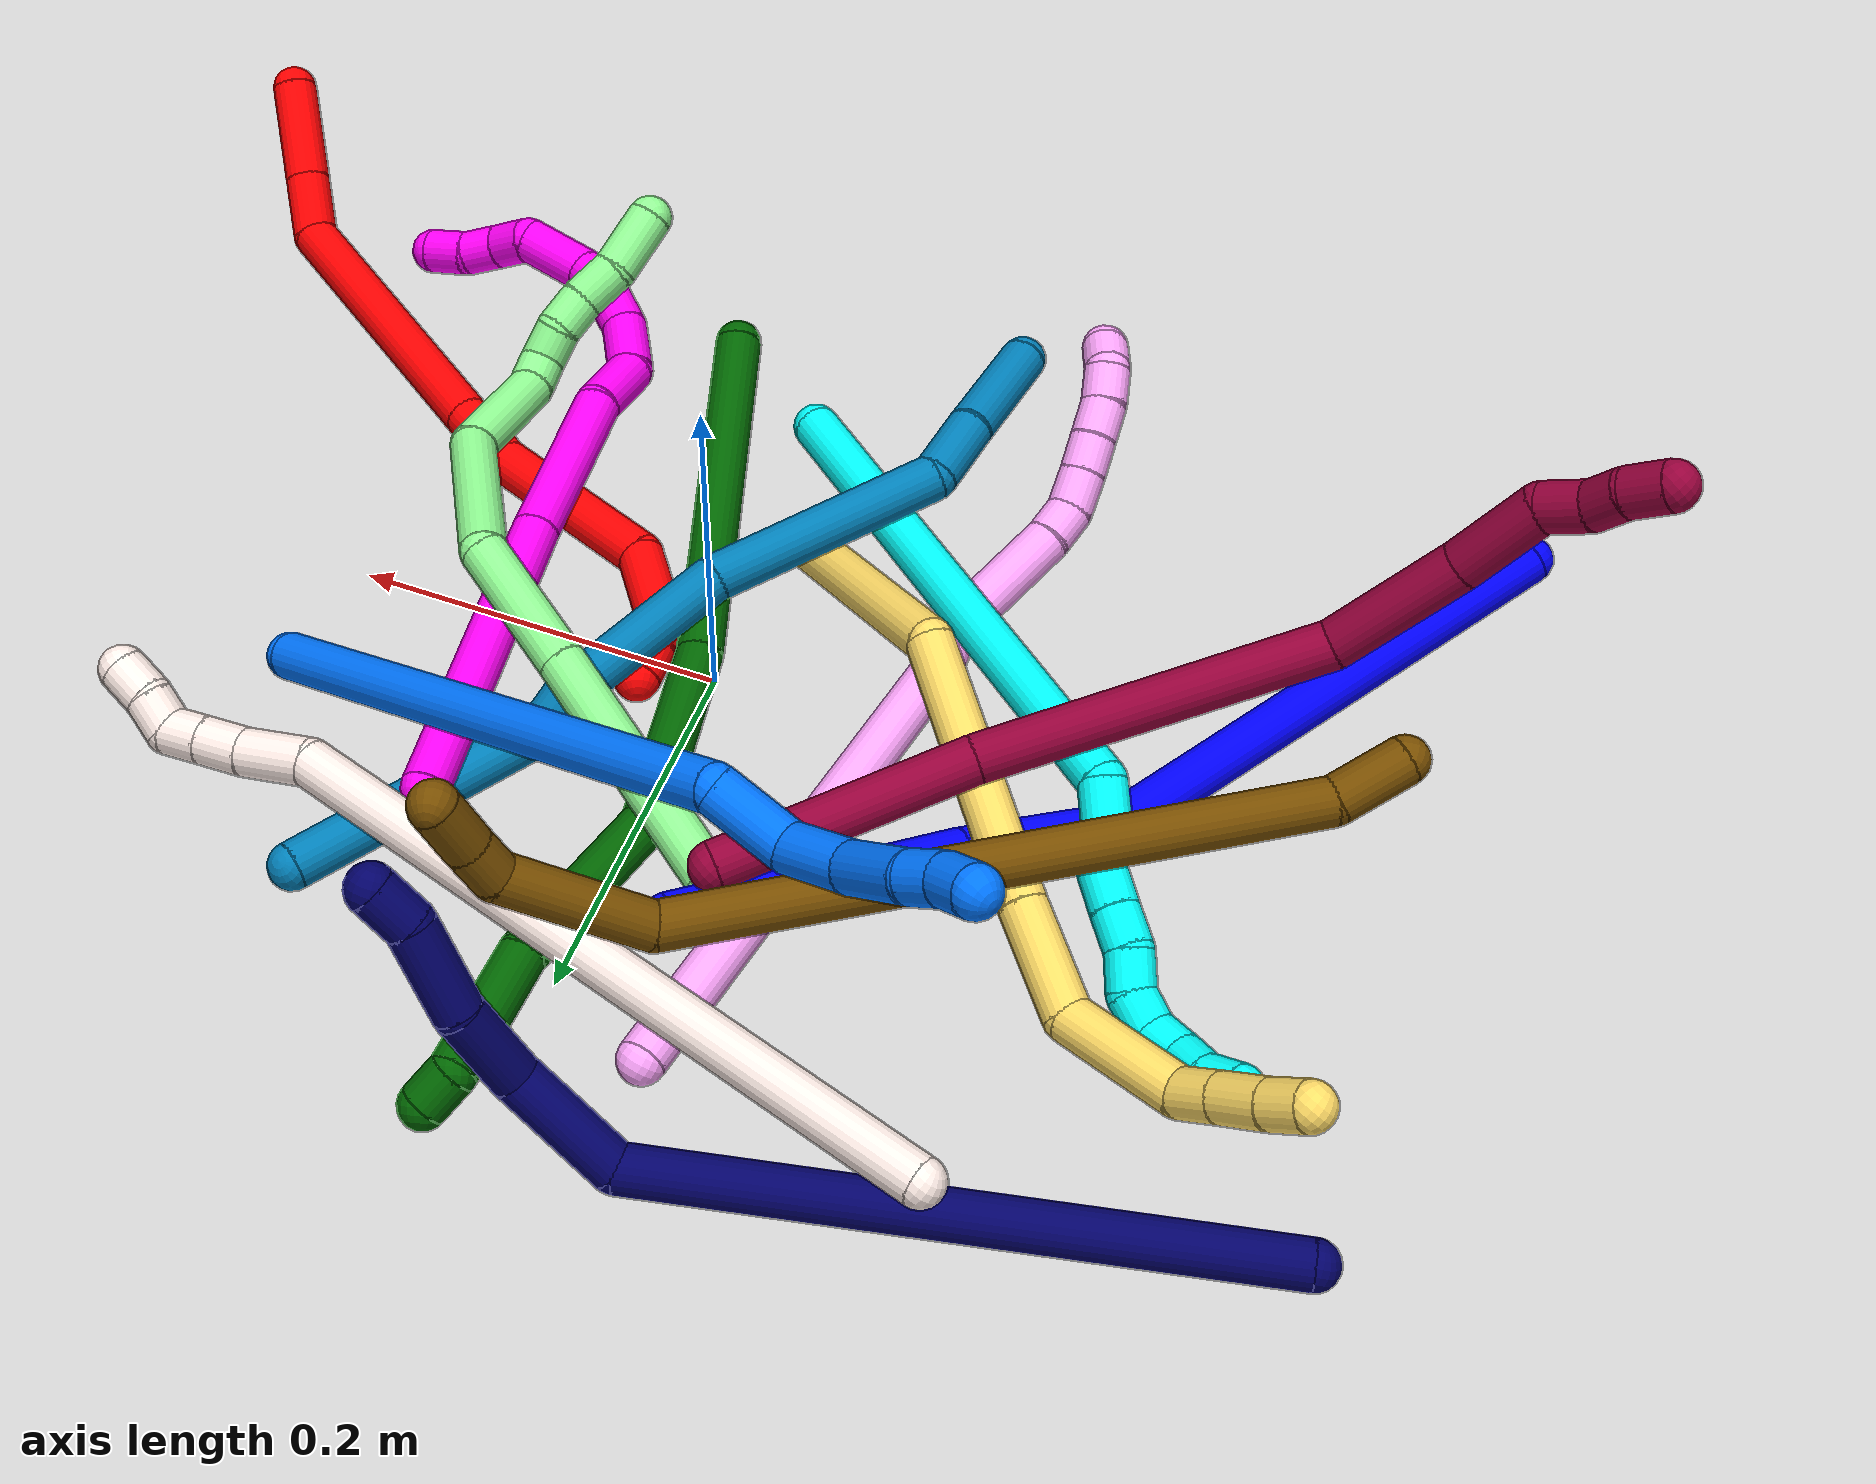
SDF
<sdf version="1.7">
 <world name="default">
  <plugin name="TubeGeneratorPlugin" filename="libtube_generator_plugin.so"/>
  <model name="photoneo_s_sensor">
   <static>1</static>
   <pose>0 0 2 1.57079 1.57079 3.14159</pose>
   <link name="link">
    <inertial><mass>0.1</mass></inertial>
    <sensor name="sensor" type="depth">
     <update_rate>30</update_rate>
     <camera>
      <horizontal_fov>1.22</horizontal_fov>
      <image><width>1920</width><height>1200</height><format>B8G8R8</format></image>
      <clip><near>0.1</near><far>4</far></clip>
      <depth_camera><output>points</output></depth_camera>
     </camera>
     <plugin name="camera_plugin" filename="libgazebo_ros_depth_camera.so">
      <baseline>0.2</baseline>
      <alwaysOn>1</alwaysOn>
      <updateRate>0.0</updateRate>
      <cameraName>camera_ir</cameraName>
      <imageTopicName>/camera/color/image_raw</imageTopicName>
      <cameraInfoTopicName>/camera/color/camera_info</cameraInfoTopicName>
      <depthImageTopicName>/camera/depth/image_raw</depthImageTopicName>
      <depthImageCameraInfoTopicName>/camera/depth/camera_info</depthImageCameraInfoTopicName>
      <pointCloudTopicName>/camera/depth/points</pointCloudTopicName>
      <frameName>fr_optical</frameName>
      <pointCloudCutoff>0.1</pointCloudCutoff>
      <pointCloudCutoffMax>2.0</pointCloudCutoffMax>
      <distortionK1>0</distortionK1>
      <distortionK2>0</distortionK2>
      <distortionK3>0</distortionK3>
      <distortionT1>0</distortionT1>
      <distortionT2>0</distortionT2>
      <CxPrime>0</CxPrime>
      <Cx>0</Cx>
      <Cy>0</Cy>
      <focalLength>0</focalLength>
      <hackBaseline>0</hackBaseline>
     </plugin>
    </sensor>
   </link>
  </model>
  <gravity>0 0 -9.8</gravity>
  <magnetic_field>6e-06 2.3e-05 -4.2e-05</magnetic_field>
  <atmosphere type="adiabatic"/>
  <physics name="default_physics" default="0" type="ode">
   <max_step_size>0.003</max_step_size>
   <real_time_factor>1</real_time_factor>
   <real_time_update_rate>1000</real_time_update_rate>
   <max_contacts>10000</max_contacts>
   <ode>
    <solver>
     <type>quick</type>
     <iters>100</iters>
     <sor>1.3</sor>
     <use_dynamic_moi_rescaling>0</use_dynamic_moi_rescaling>
    </solver>
    <constraints>
     <contact_max_correcting_vel>0</contact_max_correcting_vel>
     <contact_surface_layer>0.001</contact_surface_layer>
     <cfm>0</cfm>
     <erp>0.2</erp>
    </constraints>
   </ode>
  </physics>
  <scene><ambient>0.4 0.4 0.4 1</ambient><background>0.7 0.7 0.7 1</background><shadows>0</shadows></scene>
  <audio><device>default</device></audio>
  <spherical_coordinates>
   <surface_model>EARTH_WGS84</surface_model>
   <latitude_deg>0</latitude_deg>
   <longitude_deg>0</longitude_deg>
   <elevation>0</elevation>
   <heading_deg>0</heading_deg>
  </spherical_coordinates>
  <model name="bin">
   <static>1</static>
   <link name="bottom">
    <collision name="collision-bottom">
     <pose>0 0 -0.01 0 -0 0</pose>
     <geometry><box><size>0.8 0.6 0.02</size></box></geometry>
     <surface>
      <friction><ode><mu>100</mu><mu2>100</mu2></ode></friction>
      <contact><collide_bitmask>65535</collide_bitmask></contact>
     </surface>
    </collision>
   </link>
   <link name="west_wall">
    <collision name="collision-west_wall">
     <pose>-0.41 0 0.1 0 -0 0</pose>
     <geometry><box><size>0.02 0.6 0.2</size></box></geometry>
     <surface>
      <friction><ode><mu>100</mu><mu2>100</mu2></ode></friction>
      <contact><collide_bitmask>65535</collide_bitmask></contact>
     </surface>
    </collision>
   </link>
   <link name="east_wall">
    <collision name="collision-east_wall">
     <pose>0.41 0 0.1 0 -0 0</pose>
     <geometry><box><size>0.02 0.6 0.2</size></box></geometry>
     <surface>
      <friction><ode><mu>100</mu><mu2>100</mu2></ode></friction>
      <contact><collide_bitmask>65535</collide_bitmask></contact>
     </surface>
    </collision>
   </link>
   <link name="south_wall">
    <collision name="collision-south_wall">
     <pose>0 -0.31 0.1 0 -0 0</pose>
     <geometry><box><size>0.8 0.02 0.2</size></box></geometry>
     <surface>
      <friction><ode><mu>100</mu><mu2>100</mu2></ode></friction>
      <contact><collide_bitmask>65535</collide_bitmask></contact>
     </surface>
    </collision>
   </link>
   <link name="north_wall">
    <collision name="collision-north_wall">
     <pose>0 0.31 0.1 0 -0 0</pose>
     <geometry><box><size>0.8 0.02 0.2</size></box></geometry>
     <surface>
      <friction><ode><mu>100</mu><mu2>100</mu2></ode></friction>
      <contact><collide_bitmask>65535</collide_bitmask></contact>
     </surface>
    </collision>
   </link>
  </model>
  <model name="1">
   <static>0</static>
   <link name="1">
    <collision name="collision-cylinder-e_1_1_4">
     <pose>0.058932 0.015919 -0.118366 -3.0079 0.458381 -2.58269</pose>
     <geometry><cylinder><radius>0.0125</radius><length>0.266359</length></cylinder></geometry>
     <surface>
      <friction><ode><mu>1.16</mu><mu2>1.16</mu2><slip1>0</slip1><slip2>0</slip2></ode></friction>
      <contact><ode><kp>1e+06</kp><kd>1</kd><max_vel>0</max_vel><min_depth>0.001</min_depth></ode></contact>
     </surface>
    </collision>
    <visual name="visual-cylinder-e_1_1_4">
     <pose>0.058932 0.015919 -0.118366 -3.0079 0.458381 -2.58269</pose>
     <geometry><cylinder><radius>0.0125</radius><length>0.266359</length></cylinder></geometry>
     <material><ambient>0 0 1 1</ambient></material>
    </visual>
    <collision name="collision-cylinder-e_2_4_5">
     <pose>0.129483 0.052421 -0.271593 -2.60824 0.279512 -0.95106</pose>
     <geometry><cylinder><radius>0.0125</radius><length>0.084236</length></cylinder></geometry>
     <surface>
      <friction><ode><mu>1.16</mu><mu2>1.16</mu2><slip1>0</slip1><slip2>0</slip2></ode></friction>
      <contact><ode><kp>1e+06</kp><kd>1</kd><max_vel>0</max_vel><min_depth>0.001</min_depth></ode></contact>
     </surface>
    </collision>
    <visual name="visual-cylinder-e_2_4_5">
     <pose>0.129483 0.052421 -0.271593 -2.60824 0.279512 -0.95106</pose>
     <geometry><cylinder><radius>0.0125</radius><length>0.084236</length></cylinder></geometry>
     <material><ambient>0 0 1 1</ambient></material>
    </visual>
    <collision name="collision-cylinder-e_3_5_6">
     <pose>0.146951 0.085204 -0.331885 -2.69431 0.204426 -0.84731</pose>
     <geometry><cylinder><radius>0.0125</radius><length>0.057613</length></cylinder></geometry>
     <surface>
      <friction><ode><mu>1.16</mu><mu2>1.16</mu2><slip1>0</slip1><slip2>0</slip2></ode></friction>
      <contact><ode><kp>1e+06</kp><kd>1</kd><max_vel>0</max_vel><min_depth>0.001</min_depth></ode></contact>
     </surface>
    </collision>
    <visual name="visual-cylinder-e_3_5_6">
     <pose>0.146951 0.085204 -0.331885 -2.69431 0.204426 -0.84731</pose>
     <geometry><cylinder><radius>0.0125</radius><length>0.057613</length></cylinder></geometry>
     <material><ambient>0 0 1 1</ambient></material>
    </visual>
    <collision name="collision-cylinder-e_4_6_7">
     <pose>0.160203 0.103632 -0.366868 -2.56373 0.575913 -1.56722</pose>
     <geometry><cylinder><radius>0.0125</radius><length>0.027191</length></cylinder></geometry>
     <surface>
      <friction><ode><mu>1.16</mu><mu2>1.16</mu2><slip1>0</slip1><slip2>0</slip2></ode></friction>
      <contact><ode><kp>1e+06</kp><kd>1</kd><max_vel>0</max_vel><min_depth>0.001</min_depth></ode></contact>
     </surface>
    </collision>
    <visual name="visual-cylinder-e_4_6_7">
     <pose>0.160203 0.103632 -0.366868 -2.56373 0.575913 -1.56722</pose>
     <geometry><cylinder><radius>0.0125</radius><length>0.027191</length></cylinder></geometry>
     <material><ambient>0 0 1 1</ambient></material>
    </visual>
    <collision name="collision-cylinder-e_5_7_8">
     <pose>0.177124 0.117147 -0.388029 -2.58112 0.606932 -1.65504</pose>
     <geometry><cylinder><radius>0.0125</radius><length>0.033375</length></cylinder></geometry>
     <surface>
      <friction><ode><mu>1.16</mu><mu2>1.16</mu2><slip1>0</slip1><slip2>0</slip2></ode></friction>
      <contact><ode><kp>1e+06</kp><kd>1</kd><max_vel>0</max_vel><min_depth>0.001</min_depth></ode></contact>
     </surface>
    </collision>
    <visual name="visual-cylinder-e_5_7_8">
     <pose>0.177124 0.117147 -0.388029 -2.58112 0.606932 -1.65504</pose>
     <geometry><cylinder><radius>0.0125</radius><length>0.033375</length></cylinder></geometry>
     <material><ambient>0 0 1 1</ambient></material>
    </visual>
    <collision name="collision-cylinder-e_6_8_2">
     <pose>0.195546 0.130984 -0.410665 -2.60556 0.606874 -1.70156</pose>
     <geometry><cylinder><radius>0.0125</radius><length>0.031225</length></cylinder></geometry>
     <surface>
      <friction><ode><mu>1.16</mu><mu2>1.16</mu2><slip1>0</slip1><slip2>0</slip2></ode></friction>
      <contact><ode><kp>1e+06</kp><kd>1</kd><max_vel>0</max_vel><min_depth>0.001</min_depth></ode></contact>
     </surface>
    </collision>
    <visual name="visual-cylinder-e_6_8_2">
     <pose>0.195546 0.130984 -0.410665 -2.60556 0.606874 -1.70156</pose>
     <geometry><cylinder><radius>0.0125</radius><length>0.031225</length></cylinder></geometry>
     <material><ambient>0 0 1 1</ambient></material>
    </visual>
    <collision name="collision-sphere-2">
     <pose>0.20445 0.137533 -0.421691 0 -0 0</pose>
     <geometry><sphere><radius>0.0125</radius></sphere></geometry>
     <surface>
      <friction><ode><mu>1.16</mu><mu2>1.16</mu2><slip1>0</slip1><slip2>0</slip2></ode></friction>
      <contact><ode><kp>1e+06</kp><kd>1</kd><max_vel>0</max_vel><min_depth>0.001</min_depth></ode></contact>
     </surface>
    </collision>
    <visual name="visual-sphere-2">
     <pose>0.20445 0.137533 -0.421691 0 -0 0</pose>
     <geometry><sphere><radius>0.0125</radius></sphere></geometry>
     <material><ambient>0 0 1 1</ambient></material>
    </visual>
    <collision name="collision-sphere-4">
     <pose>0.117863 0.031838 -0.236732 0 -0 0</pose>
     <geometry><sphere><radius>0.0125</radius></sphere></geometry>
     <surface>
      <friction><ode><mu>1.16</mu><mu2>1.16</mu2><slip1>0</slip1><slip2>0</slip2></ode></friction>
      <contact><ode><kp>1e+06</kp><kd>1</kd><max_vel>0</max_vel><min_depth>0.001</min_depth></ode></contact>
     </surface>
    </collision>
    <visual name="visual-sphere-4">
     <pose>0.117863 0.031838 -0.236732 0 -0 0</pose>
     <geometry><sphere><radius>0.0125</radius></sphere></geometry>
     <material><ambient>0 0 1 1</ambient></material>
    </visual>
    <collision name="collision-sphere-1">
     <geometry><sphere><radius>0.0125</radius></sphere></geometry>
     <surface>
      <friction><ode><mu>1.16</mu><mu2>1.16</mu2><slip1>0</slip1><slip2>0</slip2></ode></friction>
      <contact><ode><kp>1e+06</kp><kd>1</kd><max_vel>0</max_vel><min_depth>0.001</min_depth></ode></contact>
     </surface>
    </collision>
    <visual name="visual-sphere-1">
     <geometry><sphere><radius>0.0125</radius></sphere></geometry>
     <material><ambient>0 0 1 1</ambient></material>
    </visual>
    <collision name="collision-sphere-8">
     <pose>0.186642 0.124434 -0.399639 0 -0 0</pose>
     <geometry><sphere><radius>0.0125</radius></sphere></geometry>
     <surface>
      <friction><ode><mu>1.16</mu><mu2>1.16</mu2><slip1>0</slip1><slip2>0</slip2></ode></friction>
      <contact><ode><kp>1e+06</kp><kd>1</kd><max_vel>0</max_vel><min_depth>0.001</min_depth></ode></contact>
     </surface>
    </collision>
    <visual name="visual-sphere-8">
     <pose>0.186642 0.124434 -0.399639 0 -0 0</pose>
     <geometry><sphere><radius>0.0125</radius></sphere></geometry>
     <material><ambient>0 0 1 1</ambient></material>
    </visual>
    <collision name="collision-sphere-5">
     <pose>0.141103 0.073004 -0.306453 0 -0 0</pose>
     <geometry><sphere><radius>0.0125</radius></sphere></geometry>
     <surface>
      <friction><ode><mu>1.16</mu><mu2>1.16</mu2><slip1>0</slip1><slip2>0</slip2></ode></friction>
      <contact><ode><kp>1e+06</kp><kd>1</kd><max_vel>0</max_vel><min_depth>0.001</min_depth></ode></contact>
     </surface>
    </collision>
    <visual name="visual-sphere-5">
     <pose>0.141103 0.073004 -0.306453 0 -0 0</pose>
     <geometry><sphere><radius>0.0125</radius></sphere></geometry>
     <material><ambient>0 0 1 1</ambient></material>
    </visual>
    <collision name="collision-sphere-6">
     <pose>0.152798 0.097404 -0.357317 0 -0 0</pose>
     <geometry><sphere><radius>0.0125</radius></sphere></geometry>
     <surface>
      <friction><ode><mu>1.16</mu><mu2>1.16</mu2><slip1>0</slip1><slip2>0</slip2></ode></friction>
      <contact><ode><kp>1e+06</kp><kd>1</kd><max_vel>0</max_vel><min_depth>0.001</min_depth></ode></contact>
     </surface>
    </collision>
    <visual name="visual-sphere-6">
     <pose>0.152798 0.097404 -0.357317 0 -0 0</pose>
     <geometry><sphere><radius>0.0125</radius></sphere></geometry>
     <material><ambient>0 0 1 1</ambient></material>
    </visual>
    <collision name="collision-sphere-7">
     <pose>0.167607 0.10986 -0.376419 0 -0 0</pose>
     <geometry><sphere><radius>0.0125</radius></sphere></geometry>
     <surface>
      <friction><ode><mu>1.16</mu><mu2>1.16</mu2><slip1>0</slip1><slip2>0</slip2></ode></friction>
      <contact><ode><kp>1e+06</kp><kd>1</kd><max_vel>0</max_vel><min_depth>0.001</min_depth></ode></contact>
     </surface>
    </collision>
    <visual name="visual-sphere-7">
     <pose>0.167607 0.10986 -0.376419 0 -0 0</pose>
     <geometry><sphere><radius>0.0125</radius></sphere></geometry>
     <material><ambient>0 0 1 1</ambient></material>
    </visual>
    <inertial>
     <pose>0.102888 0.048765 -0.218552 0 -0 0</pose>
     <mass>0.5</mass>
     <inertia>
      <ixx>-0.001966</ixx>
      <ixy>0</ixy>
      <ixz>0</ixz>
      <iyy>0.000548</iyy>
      <iyz>0</iyz>
      <izz>-0.000987</izz>
     </inertia>
    </inertial>
   </link>
   <pose>-0.376897 -0.193649 0.04486 1.90108 0.944526 0.016253</pose>
  </model>
  <model name="2">
   <static>0</static>
   <link name="2">
    <collision name="collision-cylinder-e_1_1_4">
     <pose>-0.006052 -0.006057 -0.028628 2.93309 -0.203959 -1.5486</pose>
     <geometry><cylinder><radius>0.0125</radius><length>0.059763</length></cylinder></geometry>
     <surface>
      <friction><ode><mu>1.16</mu><mu2>1.16</mu2><slip1>0</slip1><slip2>0</slip2></ode></friction>
      <contact><ode><kp>1e+06</kp><kd>1</kd><max_vel>0</max_vel><min_depth>0.001</min_depth></ode></contact>
     </surface>
    </collision>
    <visual name="visual-cylinder-e_1_1_4">
     <pose>-0.006052 -0.006057 -0.028628 2.93309 -0.203959 -1.5486</pose>
     <geometry><cylinder><radius>0.0125</radius><length>0.059763</length></cylinder></geometry>
     <material><ambient>1 0 0 1</ambient></material>
    </visual>
    <collision name="collision-cylinder-e_2_4_5">
     <pose>-0.015595 -0.01518 -0.074829 2.9689 -0.193214 -1.6835</pose>
     <geometry><cylinder><radius>0.0125</radius><length>0.036353</length></cylinder></geometry>
     <surface>
      <friction><ode><mu>1.16</mu><mu2>1.16</mu2><slip1>0</slip1><slip2>0</slip2></ode></friction>
      <contact><ode><kp>1e+06</kp><kd>1</kd><max_vel>0</max_vel><min_depth>0.001</min_depth></ode></contact>
     </surface>
    </collision>
    <visual name="visual-cylinder-e_2_4_5">
     <pose>-0.015595 -0.01518 -0.074829 2.9689 -0.193214 -1.6835</pose>
     <geometry><cylinder><radius>0.0125</radius><length>0.036353</length></cylinder></geometry>
     <material><ambient>1 0 0 1</ambient></material>
    </visual>
    <collision name="collision-cylinder-e_3_5_6">
     <pose>-0.057351 0.008394 -0.166332 -2.79575 -0.453158 1.84485</pose>
     <geometry><cylinder><radius>0.0125</radius><length>0.174808</length></cylinder></geometry>
     <surface>
      <friction><ode><mu>1.16</mu><mu2>1.16</mu2><slip1>0</slip1><slip2>0</slip2></ode></friction>
      <contact><ode><kp>1e+06</kp><kd>1</kd><max_vel>0</max_vel><min_depth>0.001</min_depth></ode></contact>
     </surface>
    </collision>
    <visual name="visual-cylinder-e_3_5_6">
     <pose>-0.057351 0.008394 -0.166332 -2.79575 -0.453158 1.84485</pose>
     <geometry><cylinder><radius>0.0125</radius><length>0.174808</length></cylinder></geometry>
     <material><ambient>1 0 0 1</ambient></material>
    </visual>
    <collision name="collision-cylinder-e_4_6_7">
     <pose>-0.104454 0.042635 -0.258341 -2.74353 -0.423297 1.63399</pose>
     <geometry><cylinder><radius>0.0125</radius><length>0.043024</length></cylinder></geometry>
     <surface>
      <friction><ode><mu>1.16</mu><mu2>1.16</mu2><slip1>0</slip1><slip2>0</slip2></ode></friction>
      <contact><ode><kp>1e+06</kp><kd>1</kd><max_vel>0</max_vel><min_depth>0.001</min_depth></ode></contact>
     </surface>
    </collision>
    <visual name="visual-cylinder-e_4_6_7">
     <pose>-0.104454 0.042635 -0.258341 -2.74353 -0.423297 1.63399</pose>
     <geometry><cylinder><radius>0.0125</radius><length>0.043024</length></cylinder></geometry>
     <material><ambient>1 0 0 1</ambient></material>
    </visual>
    <collision name="collision-cylinder-e_5_7_8">
     <pose>-0.144526 0.068977 -0.312462 -2.66212 -0.655521 1.89501</pose>
     <geometry><cylinder><radius>0.0125</radius><length>0.102484</length></cylinder></geometry>
     <surface>
      <friction><ode><mu>1.16</mu><mu2>1.16</mu2><slip1>0</slip1><slip2>0</slip2></ode></friction>
      <contact><ode><kp>1e+06</kp><kd>1</kd><max_vel>0</max_vel><min_depth>0.001</min_depth></ode></contact>
     </surface>
    </collision>
    <visual name="visual-cylinder-e_5_7_8">
     <pose>-0.144526 0.068977 -0.312462 -2.66212 -0.655521 1.89501</pose>
     <geometry><cylinder><radius>0.0125</radius><length>0.102484</length></cylinder></geometry>
     <material><ambient>1 0 0 1</ambient></material>
    </visual>
    <collision name="collision-cylinder-e_6_8_9">
     <pose>-0.179109 0.091489 -0.369082 -2.96024 -0.158654 1.43683</pose>
     <geometry><cylinder><radius>0.0125</radius><length>0.042378</length></cylinder></geometry>
     <surface>
      <friction><ode><mu>1.16</mu><mu2>1.16</mu2><slip1>0</slip1><slip2>0</slip2></ode></friction>
      <contact><ode><kp>1e+06</kp><kd>1</kd><max_vel>0</max_vel><min_depth>0.001</min_depth></ode></contact>
     </surface>
    </collision>
    <visual name="visual-cylinder-e_6_8_9">
     <pose>-0.179109 0.091489 -0.369082 -2.96024 -0.158654 1.43683</pose>
     <geometry><cylinder><radius>0.0125</radius><length>0.042378</length></cylinder></geometry>
     <material><ambient>1 0 0 1</ambient></material>
    </visual>
    <collision name="collision-cylinder-e_7_9_10">
     <pose>-0.180292 0.094973 -0.399547 3.11229 0.215528 2.87233</pose>
     <geometry><cylinder><radius>0.0125</radius><length>0.020247</length></cylinder></geometry>
     <surface>
      <friction><ode><mu>1.16</mu><mu2>1.16</mu2><slip1>0</slip1><slip2>0</slip2></ode></friction>
      <contact><ode><kp>1e+06</kp><kd>1</kd><max_vel>0</max_vel><min_depth>0.001</min_depth></ode></contact>
     </surface>
    </collision>
    <visual name="visual-cylinder-e_7_9_10">
     <pose>-0.180292 0.094973 -0.399547 3.11229 0.215528 2.87233</pose>
     <geometry><cylinder><radius>0.0125</radius><length>0.020247</length></cylinder></geometry>
     <material><ambient>1 0 0 1</ambient></material>
    </visual>
    <collision name="collision-cylinder-e_8_10_2">
     <pose>-0.173798 0.094655 -0.418967 3.13862 0.426191 3.12784</pose>
     <geometry><cylinder><radius>0.0125</radius><length>0.020942</length></cylinder></geometry>
     <surface>
      <friction><ode><mu>1.16</mu><mu2>1.16</mu2><slip1>0</slip1><slip2>0</slip2></ode></friction>
      <contact><ode><kp>1e+06</kp><kd>1</kd><max_vel>0</max_vel><min_depth>0.001</min_depth></ode></contact>
     </surface>
    </collision>
    <visual name="visual-cylinder-e_8_10_2">
     <pose>-0.173798 0.094655 -0.418967 3.13862 0.426191 3.12784</pose>
     <geometry><cylinder><radius>0.0125</radius><length>0.020942</length></cylinder></geometry>
     <material><ambient>1 0 0 1</ambient></material>
    </visual>
    <collision name="collision-sphere-2">
     <pose>-0.169469 0.094627 -0.428501 0 -0 0</pose>
     <geometry><sphere><radius>0.0125</radius></sphere></geometry>
     <surface>
      <friction><ode><mu>1.16</mu><mu2>1.16</mu2><slip1>0</slip1><slip2>0</slip2></ode></friction>
      <contact><ode><kp>1e+06</kp><kd>1</kd><max_vel>0</max_vel><min_depth>0.001</min_depth></ode></contact>
     </surface>
    </collision>
    <visual name="visual-sphere-2">
     <pose>-0.169469 0.094627 -0.428501 0 -0 0</pose>
     <geometry><sphere><radius>0.0125</radius></sphere></geometry>
     <material><ambient>1 0 0 1</ambient></material>
    </visual>
    <collision name="collision-sphere-10">
     <pose>-0.178127 0.094684 -0.409432 0 -0 0</pose>
     <geometry><sphere><radius>0.0125</radius></sphere></geometry>
     <surface>
      <friction><ode><mu>1.16</mu><mu2>1.16</mu2><slip1>0</slip1><slip2>0</slip2></ode></friction>
      <contact><ode><kp>1e+06</kp><kd>1</kd><max_vel>0</max_vel><min_depth>0.001</min_depth></ode></contact>
     </surface>
    </collision>
    <visual name="visual-sphere-10">
     <pose>-0.178127 0.094684 -0.409432 0 -0 0</pose>
     <geometry><sphere><radius>0.0125</radius></sphere></geometry>
     <material><ambient>1 0 0 1</ambient></material>
    </visual>
    <collision name="collision-sphere-9">
     <pose>-0.182457 0.095263 -0.389662 0 -0 0</pose>
     <geometry><sphere><radius>0.0125</radius></sphere></geometry>
     <surface>
      <friction><ode><mu>1.16</mu><mu2>1.16</mu2><slip1>0</slip1><slip2>0</slip2></ode></friction>
      <contact><ode><kp>1e+06</kp><kd>1</kd><max_vel>0</max_vel><min_depth>0.001</min_depth></ode></contact>
     </surface>
    </collision>
    <visual name="visual-sphere-9">
     <pose>-0.182457 0.095263 -0.389662 0 -0 0</pose>
     <geometry><sphere><radius>0.0125</radius></sphere></geometry>
     <material><ambient>1 0 0 1</ambient></material>
    </visual>
    <collision name="collision-sphere-4">
     <pose>-0.012105 -0.012114 -0.057256 0 -0 0</pose>
     <geometry><sphere><radius>0.0125</radius></sphere></geometry>
     <surface>
      <friction><ode><mu>1.16</mu><mu2>1.16</mu2><slip1>0</slip1><slip2>0</slip2></ode></friction>
      <contact><ode><kp>1e+06</kp><kd>1</kd><max_vel>0</max_vel><min_depth>0.001</min_depth></ode></contact>
     </surface>
    </collision>
    <visual name="visual-sphere-4">
     <pose>-0.012105 -0.012114 -0.057256 0 -0 0</pose>
     <geometry><sphere><radius>0.0125</radius></sphere></geometry>
     <material><ambient>1 0 0 1</ambient></material>
    </visual>
    <collision name="collision-sphere-1">
     <geometry><sphere><radius>0.0125</radius></sphere></geometry>
     <surface>
      <friction><ode><mu>1.16</mu><mu2>1.16</mu2><slip1>0</slip1><slip2>0</slip2></ode></friction>
      <contact><ode><kp>1e+06</kp><kd>1</kd><max_vel>0</max_vel><min_depth>0.001</min_depth></ode></contact>
     </surface>
    </collision>
    <visual name="visual-sphere-1">
     <geometry><sphere><radius>0.0125</radius></sphere></geometry>
     <material><ambient>1 0 0 1</ambient></material>
    </visual>
    <collision name="collision-sphere-8">
     <pose>-0.175762 0.087716 -0.348502 0 -0 0</pose>
     <geometry><sphere><radius>0.0125</radius></sphere></geometry>
     <surface>
      <friction><ode><mu>1.16</mu><mu2>1.16</mu2><slip1>0</slip1><slip2>0</slip2></ode></friction>
      <contact><ode><kp>1e+06</kp><kd>1</kd><max_vel>0</max_vel><min_depth>0.001</min_depth></ode></contact>
     </surface>
    </collision>
    <visual name="visual-sphere-8">
     <pose>-0.175762 0.087716 -0.348502 0 -0 0</pose>
     <geometry><sphere><radius>0.0125</radius></sphere></geometry>
     <material><ambient>1 0 0 1</ambient></material>
    </visual>
    <collision name="collision-sphere-5">
     <pose>-0.019085 -0.018245 -0.092402 0 -0 0</pose>
     <geometry><sphere><radius>0.0125</radius></sphere></geometry>
     <surface>
      <friction><ode><mu>1.16</mu><mu2>1.16</mu2><slip1>0</slip1><slip2>0</slip2></ode></friction>
      <contact><ode><kp>1e+06</kp><kd>1</kd><max_vel>0</max_vel><min_depth>0.001</min_depth></ode></contact>
     </surface>
    </collision>
    <visual name="visual-sphere-5">
     <pose>-0.019085 -0.018245 -0.092402 0 -0 0</pose>
     <geometry><sphere><radius>0.0125</radius></sphere></geometry>
     <material><ambient>1 0 0 1</ambient></material>
    </visual>
    <collision name="collision-sphere-6">
     <pose>-0.095617 0.035032 -0.240261 0 -0 0</pose>
     <geometry><sphere><radius>0.0125</radius></sphere></geometry>
     <surface>
      <friction><ode><mu>1.16</mu><mu2>1.16</mu2><slip1>0</slip1><slip2>0</slip2></ode></friction>
      <contact><ode><kp>1e+06</kp><kd>1</kd><max_vel>0</max_vel><min_depth>0.001</min_depth></ode></contact>
     </surface>
    </collision>
    <visual name="visual-sphere-6">
     <pose>-0.095617 0.035032 -0.240261 0 -0 0</pose>
     <geometry><sphere><radius>0.0125</radius></sphere></geometry>
     <material><ambient>1 0 0 1</ambient></material>
    </visual>
    <collision name="collision-sphere-7">
     <pose>-0.11329 0.050237 -0.276421 0 -0 0</pose>
     <geometry><sphere><radius>0.0125</radius></sphere></geometry>
     <surface>
      <friction><ode><mu>1.16</mu><mu2>1.16</mu2><slip1>0</slip1><slip2>0</slip2></ode></friction>
      <contact><ode><kp>1e+06</kp><kd>1</kd><max_vel>0</max_vel><min_depth>0.001</min_depth></ode></contact>
     </surface>
    </collision>
    <visual name="visual-sphere-7">
     <pose>-0.11329 0.050237 -0.276421 0 -0 0</pose>
     <geometry><sphere><radius>0.0125</radius></sphere></geometry>
     <material><ambient>1 0 0 1</ambient></material>
    </visual>
    <inertial>
     <pose>-0.090281 0.034478 -0.218299 0 -0 0</pose>
     <mass>0.5</mass>
     <inertia>
      <ixx>0.000303</ixx>
      <ixy>0</ixy>
      <ixz>0</ixz>
      <iyy>0.000696</iyy>
      <iyz>0</iyz>
      <izz>5.9e-05</izz>
     </inertia>
    </inertial>
   </link>
   <pose>0.388147 -0.28752 0.051485 1.4013 -0.360056 0.491936</pose>
  </model>
  <model name="3">
   <static>0</static>
   <link name="3">
    <collision name="collision-cylinder-e_1_1_4">
     <pose>0.049361 0.144516 0.034163 -1.33866 0.320911 -0.25471</pose>
     <geometry><cylinder><radius>0.0125</radius><length>0.312975</length></cylinder></geometry>
     <surface>
      <friction><ode><mu>1.16</mu><mu2>1.16</mu2><slip1>0</slip1><slip2>0</slip2></ode></friction>
      <contact><ode><kp>1e+06</kp><kd>1</kd><max_vel>0</max_vel><min_depth>0.001</min_depth></ode></contact>
     </surface>
    </collision>
    <visual name="visual-cylinder-e_1_1_4">
     <pose>0.049361 0.144516 0.034163 -1.33866 0.320911 -0.25471</pose>
     <geometry><cylinder><radius>0.0125</radius><length>0.312975</length></cylinder></geometry>
     <material><ambient>0.003922 1 0.996078 1</ambient></material>
    </visual>
    <collision name="collision-cylinder-e_2_4_5">
     <pose>0.108616 0.295566 0.069815 -1.34676 0.975387 -0.800622</pose>
     <geometry><cylinder><radius>0.0125</radius><length>0.023901</length></cylinder></geometry>
     <surface>
      <friction><ode><mu>1.16</mu><mu2>1.16</mu2><slip1>0</slip1><slip2>0</slip2></ode></friction>
      <contact><ode><kp>1e+06</kp><kd>1</kd><max_vel>0</max_vel><min_depth>0.001</min_depth></ode></contact>
     </surface>
    </collision>
    <visual name="visual-cylinder-e_2_4_5">
     <pose>0.108616 0.295566 0.069815 -1.34676 0.975387 -0.800622</pose>
     <geometry><cylinder><radius>0.0125</radius><length>0.023901</length></cylinder></geometry>
     <material><ambient>0.003922 1 0.996078 1</ambient></material>
    </visual>
    <collision name="collision-cylinder-e_3_5_6">
     <pose>0.128195 0.304682 0.071521 -1.48694 1.30948 -1.22933</pose>
     <geometry><cylinder><radius>0.0125</radius><length>0.02005</length></cylinder></geometry>
     <surface>
      <friction><ode><mu>1.16</mu><mu2>1.16</mu2><slip1>0</slip1><slip2>0</slip2></ode></friction>
      <contact><ode><kp>1e+06</kp><kd>1</kd><max_vel>0</max_vel><min_depth>0.001</min_depth></ode></contact>
     </surface>
    </collision>
    <visual name="visual-cylinder-e_3_5_6">
     <pose>0.128195 0.304682 0.071521 -1.48694 1.30948 -1.22933</pose>
     <geometry><cylinder><radius>0.0125</radius><length>0.02005</length></cylinder></geometry>
     <material><ambient>0.003922 1 0.996078 1</ambient></material>
    </visual>
    <collision name="collision-cylinder-e_4_6_7">
     <pose>0.145014 0.314894 0.0728 -1.43239 0.746996 -0.657425</pose>
     <geometry><cylinder><radius>0.0125</radius><length>0.021001</length></cylinder></geometry>
     <surface>
      <friction><ode><mu>1.16</mu><mu2>1.16</mu2><slip1>0</slip1><slip2>0</slip2></ode></friction>
      <contact><ode><kp>1e+06</kp><kd>1</kd><max_vel>0</max_vel><min_depth>0.001</min_depth></ode></contact>
     </surface>
    </collision>
    <visual name="visual-cylinder-e_4_6_7">
     <pose>0.145014 0.314894 0.0728 -1.43239 0.746996 -0.657425</pose>
     <geometry><cylinder><radius>0.0125</radius><length>0.021001</length></cylinder></geometry>
     <material><ambient>0.003922 1 0.996078 1</ambient></material>
    </visual>
    <collision name="collision-cylinder-e_5_7_8">
     <pose>0.159158 0.330156 0.07455 -1.4811 0.740952 -0.682327</pose>
     <geometry><cylinder><radius>0.0125</radius><length>0.020769</length></cylinder></geometry>
     <surface>
      <friction><ode><mu>1.16</mu><mu2>1.16</mu2><slip1>0</slip1><slip2>0</slip2></ode></friction>
      <contact><ode><kp>1e+06</kp><kd>1</kd><max_vel>0</max_vel><min_depth>0.001</min_depth></ode></contact>
     </surface>
    </collision>
    <visual name="visual-cylinder-e_5_7_8">
     <pose>0.159158 0.330156 0.07455 -1.4811 0.740952 -0.682327</pose>
     <geometry><cylinder><radius>0.0125</radius><length>0.020769</length></cylinder></geometry>
     <material><ambient>0.003922 1 0.996078 1</ambient></material>
    </visual>
    <collision name="collision-cylinder-e_6_8_9">
     <pose>0.175221 0.342971 0.076344 -1.36024 1.04113 -0.868422</pose>
     <geometry><cylinder><radius>0.0125</radius><length>0.020984</length></cylinder></geometry>
     <surface>
      <friction><ode><mu>1.16</mu><mu2>1.16</mu2><slip1>0</slip1><slip2>0</slip2></ode></friction>
      <contact><ode><kp>1e+06</kp><kd>1</kd><max_vel>0</max_vel><min_depth>0.001</min_depth></ode></contact>
     </surface>
    </collision>
    <visual name="visual-cylinder-e_6_8_9">
     <pose>0.175221 0.342971 0.076344 -1.36024 1.04113 -0.868422</pose>
     <geometry><cylinder><radius>0.0125</radius><length>0.020984</length></cylinder></geometry>
     <material><ambient>0.003922 1 0.996078 1</ambient></material>
    </visual>
    <collision name="collision-cylinder-e_7_9_10">
     <pose>0.190422 0.356057 0.076628 -1.6747 0.658404 -0.724738</pose>
     <geometry><cylinder><radius>0.0125</radius><length>0.020089</length></cylinder></geometry>
     <surface>
      <friction><ode><mu>1.16</mu><mu2>1.16</mu2><slip1>0</slip1><slip2>0</slip2></ode></friction>
      <contact><ode><kp>1e+06</kp><kd>1</kd><max_vel>0</max_vel><min_depth>0.001</min_depth></ode></contact>
     </surface>
    </collision>
    <visual name="visual-cylinder-e_7_9_10">
     <pose>0.190422 0.356057 0.076628 -1.6747 0.658404 -0.724738</pose>
     <geometry><cylinder><radius>0.0125</radius><length>0.020089</length></cylinder></geometry>
     <material><ambient>0.003922 1 0.996078 1</ambient></material>
    </visual>
    <collision name="collision-cylinder-e_8_10_11">
     <pose>0.198427 0.37384 0.076309 -1.51971 0.18575 -0.176544</pose>
     <geometry><cylinder><radius>0.0125</radius><length>0.020134</length></cylinder></geometry>
     <surface>
      <friction><ode><mu>1.16</mu><mu2>1.16</mu2><slip1>0</slip1><slip2>0</slip2></ode></friction>
      <contact><ode><kp>1e+06</kp><kd>1</kd><max_vel>0</max_vel><min_depth>0.001</min_depth></ode></contact>
     </surface>
    </collision>
    <visual name="visual-cylinder-e_8_10_11">
     <pose>0.198427 0.37384 0.076309 -1.51971 0.18575 -0.176544</pose>
     <geometry><cylinder><radius>0.0125</radius><length>0.020134</length></cylinder></geometry>
     <material><ambient>0.003922 1 0.996078 1</ambient></material>
    </visual>
    <collision name="collision-cylinder-e_9_11_12">
     <pose>0.201231 0.39312 0.080189 -1.22605 0.094396 -0.066426</pose>
     <geometry><cylinder><radius>0.0125</radius><length>0.020063</length></cylinder></geometry>
     <surface>
      <friction><ode><mu>1.16</mu><mu2>1.16</mu2><slip1>0</slip1><slip2>0</slip2></ode></friction>
      <contact><ode><kp>1e+06</kp><kd>1</kd><max_vel>0</max_vel><min_depth>0.001</min_depth></ode></contact>
     </surface>
    </collision>
    <visual name="visual-cylinder-e_9_11_12">
     <pose>0.201231 0.39312 0.080189 -1.22605 0.094396 -0.066426</pose>
     <geometry><cylinder><radius>0.0125</radius><length>0.020063</length></cylinder></geometry>
     <material><ambient>0.003922 1 0.996078 1</ambient></material>
    </visual>
    <collision name="collision-cylinder-e_10_12_2">
     <pose>0.200341 0.412327 0.084441 -1.48164 -0.184341 0.168676</pose>
     <geometry><cylinder><radius>0.0125</radius><length>0.020034</length></cylinder></geometry>
     <surface>
      <friction><ode><mu>1.16</mu><mu2>1.16</mu2><slip1>0</slip1><slip2>0</slip2></ode></friction>
      <contact><ode><kp>1e+06</kp><kd>1</kd><max_vel>0</max_vel><min_depth>0.001</min_depth></ode></contact>
     </surface>
    </collision>
    <visual name="visual-cylinder-e_10_12_2">
     <pose>0.200341 0.412327 0.084441 -1.48164 -0.184341 0.168676</pose>
     <geometry><cylinder><radius>0.0125</radius><length>0.020034</length></cylinder></geometry>
     <material><ambient>0.003922 1 0.996078 1</ambient></material>
    </visual>
    <collision name="collision-sphere-2">
     <pose>0.198505 0.422136 0.085318 0 -0 0</pose>
     <geometry><sphere><radius>0.0125</radius></sphere></geometry>
     <surface>
      <friction><ode><mu>1.16</mu><mu2>1.16</mu2><slip1>0</slip1><slip2>0</slip2></ode></friction>
      <contact><ode><kp>1e+06</kp><kd>1</kd><max_vel>0</max_vel><min_depth>0.001</min_depth></ode></contact>
     </surface>
    </collision>
    <visual name="visual-sphere-2">
     <pose>0.198505 0.422136 0.085318 0 -0 0</pose>
     <geometry><sphere><radius>0.0125</radius></sphere></geometry>
     <material><ambient>0.003922 1 0.996078 1</ambient></material>
    </visual>
    <collision name="collision-sphere-12">
     <pose>0.202177 0.402519 0.083565 0 -0 0</pose>
     <geometry><sphere><radius>0.0125</radius></sphere></geometry>
     <surface>
      <friction><ode><mu>1.16</mu><mu2>1.16</mu2><slip1>0</slip1><slip2>0</slip2></ode></friction>
      <contact><ode><kp>1e+06</kp><kd>1</kd><max_vel>0</max_vel><min_depth>0.001</min_depth></ode></contact>
     </surface>
    </collision>
    <visual name="visual-sphere-12">
     <pose>0.202177 0.402519 0.083565 0 -0 0</pose>
     <geometry><sphere><radius>0.0125</radius></sphere></geometry>
     <material><ambient>0.003922 1 0.996078 1</ambient></material>
    </visual>
    <collision name="collision-sphere-11">
     <pose>0.200286 0.383721 0.076814 0 -0 0</pose>
     <geometry><sphere><radius>0.0125</radius></sphere></geometry>
     <surface>
      <friction><ode><mu>1.16</mu><mu2>1.16</mu2><slip1>0</slip1><slip2>0</slip2></ode></friction>
      <contact><ode><kp>1e+06</kp><kd>1</kd><max_vel>0</max_vel><min_depth>0.001</min_depth></ode></contact>
     </surface>
    </collision>
    <visual name="visual-sphere-11">
     <pose>0.200286 0.383721 0.076814 0 -0 0</pose>
     <geometry><sphere><radius>0.0125</radius></sphere></geometry>
     <material><ambient>0.003922 1 0.996078 1</ambient></material>
    </visual>
    <collision name="collision-sphere-10">
     <pose>0.196567 0.363959 0.075804 0 -0 0</pose>
     <geometry><sphere><radius>0.0125</radius></sphere></geometry>
     <surface>
      <friction><ode><mu>1.16</mu><mu2>1.16</mu2><slip1>0</slip1><slip2>0</slip2></ode></friction>
      <contact><ode><kp>1e+06</kp><kd>1</kd><max_vel>0</max_vel><min_depth>0.001</min_depth></ode></contact>
     </surface>
    </collision>
    <visual name="visual-sphere-10">
     <pose>0.196567 0.363959 0.075804 0 -0 0</pose>
     <geometry><sphere><radius>0.0125</radius></sphere></geometry>
     <material><ambient>0.003922 1 0.996078 1</ambient></material>
    </visual>
    <collision name="collision-sphere-9">
     <pose>0.184276 0.348155 0.077452 0 -0 0</pose>
     <geometry><sphere><radius>0.0125</radius></sphere></geometry>
     <surface>
      <friction><ode><mu>1.16</mu><mu2>1.16</mu2><slip1>0</slip1><slip2>0</slip2></ode></friction>
      <contact><ode><kp>1e+06</kp><kd>1</kd><max_vel>0</max_vel><min_depth>0.001</min_depth></ode></contact>
     </surface>
    </collision>
    <visual name="visual-sphere-9">
     <pose>0.184276 0.348155 0.077452 0 -0 0</pose>
     <geometry><sphere><radius>0.0125</radius></sphere></geometry>
     <material><ambient>0.003922 1 0.996078 1</ambient></material>
    </visual>
    <collision name="collision-sphere-4">
     <pose>0.098722 0.289031 0.068325 0 -0 0</pose>
     <geometry><sphere><radius>0.0125</radius></sphere></geometry>
     <surface>
      <friction><ode><mu>1.16</mu><mu2>1.16</mu2><slip1>0</slip1><slip2>0</slip2></ode></friction>
      <contact><ode><kp>1e+06</kp><kd>1</kd><max_vel>0</max_vel><min_depth>0.001</min_depth></ode></contact>
     </surface>
    </collision>
    <visual name="visual-sphere-4">
     <pose>0.098722 0.289031 0.068325 0 -0 0</pose>
     <geometry><sphere><radius>0.0125</radius></sphere></geometry>
     <material><ambient>0.003922 1 0.996078 1</ambient></material>
    </visual>
    <collision name="collision-sphere-1">
     <geometry><sphere><radius>0.0125</radius></sphere></geometry>
     <surface>
      <friction><ode><mu>1.16</mu><mu2>1.16</mu2><slip1>0</slip1><slip2>0</slip2></ode></friction>
      <contact><ode><kp>1e+06</kp><kd>1</kd><max_vel>0</max_vel><min_depth>0.001</min_depth></ode></contact>
     </surface>
    </collision>
    <visual name="visual-sphere-1">
     <geometry><sphere><radius>0.0125</radius></sphere></geometry>
     <material><ambient>0.003922 1 0.996078 1</ambient></material>
    </visual>
    <collision name="collision-sphere-8">
     <pose>0.166167 0.337787 0.075236 0 -0 0</pose>
     <geometry><sphere><radius>0.0125</radius></sphere></geometry>
     <surface>
      <friction><ode><mu>1.16</mu><mu2>1.16</mu2><slip1>0</slip1><slip2>0</slip2></ode></friction>
      <contact><ode><kp>1e+06</kp><kd>1</kd><max_vel>0</max_vel><min_depth>0.001</min_depth></ode></contact>
     </surface>
    </collision>
    <visual name="visual-sphere-8">
     <pose>0.166167 0.337787 0.075236 0 -0 0</pose>
     <geometry><sphere><radius>0.0125</radius></sphere></geometry>
     <material><ambient>0.003922 1 0.996078 1</ambient></material>
    </visual>
    <collision name="collision-sphere-5">
     <pose>0.11851 0.302101 0.071304 0 -0 0</pose>
     <geometry><sphere><radius>0.0125</radius></sphere></geometry>
     <surface>
      <friction><ode><mu>1.16</mu><mu2>1.16</mu2><slip1>0</slip1><slip2>0</slip2></ode></friction>
      <contact><ode><kp>1e+06</kp><kd>1</kd><max_vel>0</max_vel><min_depth>0.001</min_depth></ode></contact>
     </surface>
    </collision>
    <visual name="visual-sphere-5">
     <pose>0.11851 0.302101 0.071304 0 -0 0</pose>
     <geometry><sphere><radius>0.0125</radius></sphere></geometry>
     <material><ambient>0.003922 1 0.996078 1</ambient></material>
    </visual>
    <collision name="collision-sphere-6">
     <pose>0.137879 0.307263 0.071737 0 -0 0</pose>
     <geometry><sphere><radius>0.0125</radius></sphere></geometry>
     <surface>
      <friction><ode><mu>1.16</mu><mu2>1.16</mu2><slip1>0</slip1><slip2>0</slip2></ode></friction>
      <contact><ode><kp>1e+06</kp><kd>1</kd><max_vel>0</max_vel><min_depth>0.001</min_depth></ode></contact>
     </surface>
    </collision>
    <visual name="visual-sphere-6">
     <pose>0.137879 0.307263 0.071737 0 -0 0</pose>
     <geometry><sphere><radius>0.0125</radius></sphere></geometry>
     <material><ambient>0.003922 1 0.996078 1</ambient></material>
    </visual>
    <collision name="collision-sphere-7">
     <pose>0.152148 0.322525 0.073863 0 -0 0</pose>
     <geometry><sphere><radius>0.0125</radius></sphere></geometry>
     <surface>
      <friction><ode><mu>1.16</mu><mu2>1.16</mu2><slip1>0</slip1><slip2>0</slip2></ode></friction>
      <contact><ode><kp>1e+06</kp><kd>1</kd><max_vel>0</max_vel><min_depth>0.001</min_depth></ode></contact>
     </surface>
    </collision>
    <visual name="visual-sphere-7">
     <pose>0.152148 0.322525 0.073863 0 -0 0</pose>
     <geometry><sphere><radius>0.0125</radius></sphere></geometry>
     <material><ambient>0.003922 1 0.996078 1</ambient></material>
    </visual>
    <inertial>
     <pose>0.093029 0.219795 0.0497 0 -0 0</pose>
     <mass>0.5</mass>
     <inertia>
      <ixx>0.001763</ixx>
      <ixy>0</ixy>
      <ixz>0</ixz>
      <iyy>0.000192</iyy>
      <iyz>0</iyz>
      <izz>-0.003191</izz>
     </inertia>
    </inertial>
   </link>
   <pose>0.012726 -0.175578 0.014402 0.349794 0.793555 1.48082</pose>
  </model>
  <model name="4">
   <static>0</static>
   <link name="4">
    <collision name="collision-cylinder-e_1_1_4">
     <pose>-0.002493 -0.082238 0.10872 0.647598 -0.018283 -0.006136</pose>
     <geometry><cylinder><radius>0.0125</radius><length>0.272685</length></cylinder></geometry>
     <surface>
      <friction><ode><mu>1.16</mu><mu2>1.16</mu2><slip1>0</slip1><slip2>0</slip2></ode></friction>
      <contact><ode><kp>1e+06</kp><kd>1</kd><max_vel>0</max_vel><min_depth>0.001</min_depth></ode></contact>
     </surface>
    </collision>
    <visual name="visual-cylinder-e_1_1_4">
     <pose>-0.002493 -0.082238 0.10872 0.647598 -0.018283 -0.006136</pose>
     <geometry><cylinder><radius>0.0125</radius><length>0.272685</length></cylinder></geometry>
     <material><ambient>1 0.65098 0.996078 1</ambient></material>
    </visual>
    <collision name="collision-cylinder-e_2_4_5">
     <pose>-0.001651 -0.177371 0.227206 0.922596 0.203303 0.101318</pose>
     <geometry><cylinder><radius>0.0125</radius><length>0.033032</length></cylinder></geometry>
     <surface>
      <friction><ode><mu>1.16</mu><mu2>1.16</mu2><slip1>0</slip1><slip2>0</slip2></ode></friction>
      <contact><ode><kp>1e+06</kp><kd>1</kd><max_vel>0</max_vel><min_depth>0.001</min_depth></ode></contact>
     </surface>
    </collision>
    <visual name="visual-cylinder-e_2_4_5">
     <pose>-0.001651 -0.177371 0.227206 0.922596 0.203303 0.101318</pose>
     <geometry><cylinder><radius>0.0125</radius><length>0.033032</length></cylinder></geometry>
     <material><ambient>1 0.65098 0.996078 1</ambient></material>
    </visual>
    <collision name="collision-cylinder-e_3_5_6">
     <pose>-0.005692 -0.205133 0.26795 0.447462 -0.211454 -0.048285</pose>
     <geometry><cylinder><radius>0.0125</radius><length>0.070286</length></cylinder></geometry>
     <surface>
      <friction><ode><mu>1.16</mu><mu2>1.16</mu2><slip1>0</slip1><slip2>0</slip2></ode></friction>
      <contact><ode><kp>1e+06</kp><kd>1</kd><max_vel>0</max_vel><min_depth>0.001</min_depth></ode></contact>
     </surface>
    </collision>
    <visual name="visual-cylinder-e_3_5_6">
     <pose>-0.005692 -0.205133 0.26795 0.447462 -0.211454 -0.048285</pose>
     <geometry><cylinder><radius>0.0125</radius><length>0.070286</length></cylinder></geometry>
     <material><ambient>1 0.65098 0.996078 1</ambient></material>
    </visual>
    <collision name="collision-cylinder-e_4_6_7">
     <pose>-0.013655 -0.225168 0.307987 0.518405 -0.056283 -0.014928</pose>
     <geometry><cylinder><radius>0.0125</radius><length>0.020893</length></cylinder></geometry>
     <surface>
      <friction><ode><mu>1.16</mu><mu2>1.16</mu2><slip1>0</slip1><slip2>0</slip2></ode></friction>
      <contact><ode><kp>1e+06</kp><kd>1</kd><max_vel>0</max_vel><min_depth>0.001</min_depth></ode></contact>
     </surface>
    </collision>
    <visual name="visual-cylinder-e_4_6_7">
     <pose>-0.013655 -0.225168 0.307987 0.518405 -0.056283 -0.014928</pose>
     <geometry><cylinder><radius>0.0125</radius><length>0.020893</length></cylinder></geometry>
     <material><ambient>1 0.65098 0.996078 1</ambient></material>
    </visual>
    <collision name="collision-cylinder-e_5_7_8">
     <pose>-0.011978 -0.232956 0.327492 0.245782 0.207317 0.025697</pose>
     <geometry><cylinder><radius>0.0125</radius><length>0.02201</length></cylinder></geometry>
     <surface>
      <friction><ode><mu>1.16</mu><mu2>1.16</mu2><slip1>0</slip1><slip2>0</slip2></ode></friction>
      <contact><ode><kp>1e+06</kp><kd>1</kd><max_vel>0</max_vel><min_depth>0.001</min_depth></ode></contact>
     </surface>
    </collision>
    <visual name="visual-cylinder-e_5_7_8">
     <pose>-0.011978 -0.232956 0.327492 0.245782 0.207317 0.025697</pose>
     <geometry><cylinder><radius>0.0125</radius><length>0.02201</length></cylinder></geometry>
     <material><ambient>1 0.65098 0.996078 1</ambient></material>
    </visual>
    <collision name="collision-cylinder-e_6_8_9">
     <pose>-0.007218 -0.238012 0.347453 0.250587 0.248687 0.031483</pose>
     <geometry><cylinder><radius>0.0125</radius><length>0.020269</length></cylinder></geometry>
     <surface>
      <friction><ode><mu>1.16</mu><mu2>1.16</mu2><slip1>0</slip1><slip2>0</slip2></ode></friction>
      <contact><ode><kp>1e+06</kp><kd>1</kd><max_vel>0</max_vel><min_depth>0.001</min_depth></ode></contact>
     </surface>
    </collision>
    <visual name="visual-cylinder-e_6_8_9">
     <pose>-0.007218 -0.238012 0.347453 0.250587 0.248687 0.031483</pose>
     <geometry><cylinder><radius>0.0125</radius><length>0.020269</length></cylinder></geometry>
     <material><ambient>1 0.65098 0.996078 1</ambient></material>
    </visual>
    <collision name="collision-cylinder-e_7_9_10">
     <pose>-0.002129 -0.243583 0.366467 0.318799 0.253858 0.041026</pose>
     <geometry><cylinder><radius>0.0125</radius><length>0.020666</length></cylinder></geometry>
     <surface>
      <friction><ode><mu>1.16</mu><mu2>1.16</mu2><slip1>0</slip1><slip2>0</slip2></ode></friction>
      <contact><ode><kp>1e+06</kp><kd>1</kd><max_vel>0</max_vel><min_depth>0.001</min_depth></ode></contact>
     </surface>
    </collision>
    <visual name="visual-cylinder-e_7_9_10">
     <pose>-0.002129 -0.243583 0.366467 0.318799 0.253858 0.041026</pose>
     <geometry><cylinder><radius>0.0125</radius><length>0.020666</length></cylinder></geometry>
     <material><ambient>1 0.65098 0.996078 1</ambient></material>
    </visual>
    <collision name="collision-cylinder-e_8_10_11">
     <pose>0.004655 -0.249604 0.384584 0.323195 0.431834 0.071482</pose>
     <geometry><cylinder><radius>0.0125</radius><length>0.020018</length></cylinder></geometry>
     <surface>
      <friction><ode><mu>1.16</mu><mu2>1.16</mu2><slip1>0</slip1><slip2>0</slip2></ode></friction>
      <contact><ode><kp>1e+06</kp><kd>1</kd><max_vel>0</max_vel><min_depth>0.001</min_depth></ode></contact>
     </surface>
    </collision>
    <visual name="visual-cylinder-e_8_10_11">
     <pose>0.004655 -0.249604 0.384584 0.323195 0.431834 0.071482</pose>
     <geometry><cylinder><radius>0.0125</radius><length>0.020018</length></cylinder></geometry>
     <material><ambient>1 0.65098 0.996078 1</ambient></material>
    </visual>
    <collision name="collision-cylinder-e_9_11_2">
     <pose>0.013574 -0.259769 0.39831 0.958988 0.488914 0.257968</pose>
     <geometry><cylinder><radius>0.0125</radius><length>0.020141</length></cylinder></geometry>
     <surface>
      <friction><ode><mu>1.16</mu><mu2>1.16</mu2><slip1>0</slip1><slip2>0</slip2></ode></friction>
      <contact><ode><kp>1e+06</kp><kd>1</kd><max_vel>0</max_vel><min_depth>0.001</min_depth></ode></contact>
     </surface>
    </collision>
    <visual name="visual-cylinder-e_9_11_2">
     <pose>0.013574 -0.259769 0.39831 0.958988 0.488914 0.257968</pose>
     <geometry><cylinder><radius>0.0125</radius><length>0.020141</length></cylinder></geometry>
     <material><ambient>1 0.65098 0.996078 1</ambient></material>
    </visual>
    <collision name="collision-sphere-2">
     <pose>0.018304 -0.267047 0.403417 0 -0 0</pose>
     <geometry><sphere><radius>0.0125</radius></sphere></geometry>
     <surface>
      <friction><ode><mu>1.16</mu><mu2>1.16</mu2><slip1>0</slip1><slip2>0</slip2></ode></friction>
      <contact><ode><kp>1e+06</kp><kd>1</kd><max_vel>0</max_vel><min_depth>0.001</min_depth></ode></contact>
     </surface>
    </collision>
    <visual name="visual-sphere-2">
     <pose>0.018304 -0.267047 0.403417 0 -0 0</pose>
     <geometry><sphere><radius>0.0125</radius></sphere></geometry>
     <material><ambient>1 0.65098 0.996078 1</ambient></material>
    </visual>
    <collision name="collision-sphere-11">
     <pose>0.008845 -0.252491 0.393204 0 -0 0</pose>
     <geometry><sphere><radius>0.0125</radius></sphere></geometry>
     <surface>
      <friction><ode><mu>1.16</mu><mu2>1.16</mu2><slip1>0</slip1><slip2>0</slip2></ode></friction>
      <contact><ode><kp>1e+06</kp><kd>1</kd><max_vel>0</max_vel><min_depth>0.001</min_depth></ode></contact>
     </surface>
    </collision>
    <visual name="visual-sphere-11">
     <pose>0.008845 -0.252491 0.393204 0 -0 0</pose>
     <geometry><sphere><radius>0.0125</radius></sphere></geometry>
     <material><ambient>1 0.65098 0.996078 1</ambient></material>
    </visual>
    <collision name="collision-sphere-10">
     <pose>0.000466 -0.246717 0.375965 0 -0 0</pose>
     <geometry><sphere><radius>0.0125</radius></sphere></geometry>
     <surface>
      <friction><ode><mu>1.16</mu><mu2>1.16</mu2><slip1>0</slip1><slip2>0</slip2></ode></friction>
      <contact><ode><kp>1e+06</kp><kd>1</kd><max_vel>0</max_vel><min_depth>0.001</min_depth></ode></contact>
     </surface>
    </collision>
    <visual name="visual-sphere-10">
     <pose>0.000466 -0.246717 0.375965 0 -0 0</pose>
     <geometry><sphere><radius>0.0125</radius></sphere></geometry>
     <material><ambient>1 0.65098 0.996078 1</ambient></material>
    </visual>
    <collision name="collision-sphere-9">
     <pose>-0.004724 -0.240448 0.356969 0 -0 0</pose>
     <geometry><sphere><radius>0.0125</radius></sphere></geometry>
     <surface>
      <friction><ode><mu>1.16</mu><mu2>1.16</mu2><slip1>0</slip1><slip2>0</slip2></ode></friction>
      <contact><ode><kp>1e+06</kp><kd>1</kd><max_vel>0</max_vel><min_depth>0.001</min_depth></ode></contact>
     </surface>
    </collision>
    <visual name="visual-sphere-9">
     <pose>-0.004724 -0.240448 0.356969 0 -0 0</pose>
     <geometry><sphere><radius>0.0125</radius></sphere></geometry>
     <material><ambient>1 0.65098 0.996078 1</ambient></material>
    </visual>
    <collision name="collision-sphere-4">
     <pose>-0.004985 -0.164476 0.21744 0 -0 0</pose>
     <geometry><sphere><radius>0.0125</radius></sphere></geometry>
     <surface>
      <friction><ode><mu>1.16</mu><mu2>1.16</mu2><slip1>0</slip1><slip2>0</slip2></ode></friction>
      <contact><ode><kp>1e+06</kp><kd>1</kd><max_vel>0</max_vel><min_depth>0.001</min_depth></ode></contact>
     </surface>
    </collision>
    <visual name="visual-sphere-4">
     <pose>-0.004985 -0.164476 0.21744 0 -0 0</pose>
     <geometry><sphere><radius>0.0125</radius></sphere></geometry>
     <material><ambient>1 0.65098 0.996078 1</ambient></material>
    </visual>
    <collision name="collision-sphere-1">
     <geometry><sphere><radius>0.0125</radius></sphere></geometry>
     <surface>
      <friction><ode><mu>1.16</mu><mu2>1.16</mu2><slip1>0</slip1><slip2>0</slip2></ode></friction>
      <contact><ode><kp>1e+06</kp><kd>1</kd><max_vel>0</max_vel><min_depth>0.001</min_depth></ode></contact>
     </surface>
    </collision>
    <visual name="visual-sphere-1">
     <geometry><sphere><radius>0.0125</radius></sphere></geometry>
     <material><ambient>1 0.65098 0.996078 1</ambient></material>
    </visual>
    <collision name="collision-sphere-8">
     <pose>-0.009713 -0.235576 0.337937 0 -0 0</pose>
     <geometry><sphere><radius>0.0125</radius></sphere></geometry>
     <surface>
      <friction><ode><mu>1.16</mu><mu2>1.16</mu2><slip1>0</slip1><slip2>0</slip2></ode></friction>
      <contact><ode><kp>1e+06</kp><kd>1</kd><max_vel>0</max_vel><min_depth>0.001</min_depth></ode></contact>
     </surface>
    </collision>
    <visual name="visual-sphere-8">
     <pose>-0.009713 -0.235576 0.337937 0 -0 0</pose>
     <geometry><sphere><radius>0.0125</radius></sphere></geometry>
     <material><ambient>1 0.65098 0.996078 1</ambient></material>
    </visual>
    <collision name="collision-sphere-5">
     <pose>0.001684 -0.190266 0.236972 0 -0 0</pose>
     <geometry><sphere><radius>0.0125</radius></sphere></geometry>
     <surface>
      <friction><ode><mu>1.16</mu><mu2>1.16</mu2><slip1>0</slip1><slip2>0</slip2></ode></friction>
      <contact><ode><kp>1e+06</kp><kd>1</kd><max_vel>0</max_vel><min_depth>0.001</min_depth></ode></contact>
     </surface>
    </collision>
    <visual name="visual-sphere-5">
     <pose>0.001684 -0.190266 0.236972 0 -0 0</pose>
     <geometry><sphere><radius>0.0125</radius></sphere></geometry>
     <material><ambient>1 0.65098 0.996078 1</ambient></material>
    </visual>
    <collision name="collision-sphere-6">
     <pose>-0.013068 -0.22 0.298927 0 -0 0</pose>
     <geometry><sphere><radius>0.0125</radius></sphere></geometry>
     <surface>
      <friction><ode><mu>1.16</mu><mu2>1.16</mu2><slip1>0</slip1><slip2>0</slip2></ode></friction>
      <contact><ode><kp>1e+06</kp><kd>1</kd><max_vel>0</max_vel><min_depth>0.001</min_depth></ode></contact>
     </surface>
    </collision>
    <visual name="visual-sphere-6">
     <pose>-0.013068 -0.22 0.298927 0 -0 0</pose>
     <geometry><sphere><radius>0.0125</radius></sphere></geometry>
     <material><ambient>1 0.65098 0.996078 1</ambient></material>
    </visual>
    <collision name="collision-sphere-7">
     <pose>-0.014243 -0.230336 0.317046 0 -0 0</pose>
     <geometry><sphere><radius>0.0125</radius></sphere></geometry>
     <surface>
      <friction><ode><mu>1.16</mu><mu2>1.16</mu2><slip1>0</slip1><slip2>0</slip2></ode></friction>
      <contact><ode><kp>1e+06</kp><kd>1</kd><max_vel>0</max_vel><min_depth>0.001</min_depth></ode></contact>
     </surface>
    </collision>
    <visual name="visual-sphere-7">
     <pose>-0.014243 -0.230336 0.317046 0 -0 0</pose>
     <geometry><sphere><radius>0.0125</radius></sphere></geometry>
     <material><ambient>1 0.65098 0.996078 1</ambient></material>
    </visual>
    <inertial>
     <pose>-0.003014 -0.145241 0.199928 0 -0 0</pose>
     <mass>0.5</mass>
     <inertia>
      <ixx>0.001734</ixx>
      <ixy>0</ixy>
      <ixz>0</ixz>
      <iyy>0.001364</iyy>
      <iyz>0</iyz>
      <izz>0.001112</izz>
     </inertia>
    </inertial>
   </link>
   <pose>-0.059204 0.22938 0.011459 0.892486 -0.172442 -0.164077</pose>
  </model>
  <model name="5">
   <static>0</static>
   <link name="5">
    <collision name="collision-cylinder-e_1_1_4">
     <pose>-0.07061 0.026908 -0.005743 -1.78107 -1.19924 1.40302</pose>
     <geometry><cylinder><radius>0.0125</radius><length>0.151563</length></cylinder></geometry>
     <surface>
      <friction><ode><mu>1.16</mu><mu2>1.16</mu2><slip1>0</slip1><slip2>0</slip2></ode></friction>
      <contact><ode><kp>1e+06</kp><kd>1</kd><max_vel>0</max_vel><min_depth>0.001</min_depth></ode></contact>
     </surface>
    </collision>
    <visual name="visual-cylinder-e_1_1_4">
     <pose>-0.07061 0.026908 -0.005743 -1.78107 -1.19924 1.40302</pose>
     <geometry><cylinder><radius>0.0125</radius><length>0.151563</length></cylinder></geometry>
     <material><ambient>1 0.858824 0.4 1</ambient></material>
    </visual>
    <collision name="collision-cylinder-e_2_4_5">
     <pose>-0.187314 0.100899 0.019898 -0.982868 -0.683574 0.376311</pose>
     <geometry><cylinder><radius>0.0125</radius><length>0.145966</length></cylinder></geometry>
     <surface>
      <friction><ode><mu>1.16</mu><mu2>1.16</mu2><slip1>0</slip1><slip2>0</slip2></ode></friction>
      <contact><ode><kp>1e+06</kp><kd>1</kd><max_vel>0</max_vel><min_depth>0.001</min_depth></ode></contact>
     </surface>
    </collision>
    <visual name="visual-cylinder-e_2_4_5">
     <pose>-0.187314 0.100899 0.019898 -0.982868 -0.683574 0.376311</pose>
     <geometry><cylinder><radius>0.0125</radius><length>0.145966</length></cylinder></geometry>
     <material><ambient>1 0.858824 0.4 1</ambient></material>
    </visual>
    <collision name="collision-cylinder-e_3_5_6">
     <pose>-0.251238 0.168125 0.062998 -1.04398 -0.653177 0.384843</pose>
     <geometry><cylinder><radius>0.0125</radius><length>0.05868</length></cylinder></geometry>
     <surface>
      <friction><ode><mu>1.16</mu><mu2>1.16</mu2><slip1>0</slip1><slip2>0</slip2></ode></friction>
      <contact><ode><kp>1e+06</kp><kd>1</kd><max_vel>0</max_vel><min_depth>0.001</min_depth></ode></contact>
     </surface>
    </collision>
    <visual name="visual-cylinder-e_3_5_6">
     <pose>-0.251238 0.168125 0.062998 -1.04398 -0.653177 0.384843</pose>
     <geometry><cylinder><radius>0.0125</radius><length>0.05868</length></cylinder></geometry>
     <material><ambient>1 0.858824 0.4 1</ambient></material>
    </visual>
    <collision name="collision-cylinder-e_4_6_7">
     <pose>-0.292863 0.211196 0.069061 -1.81245 -0.789149 0.977069</pose>
     <geometry><cylinder><radius>0.0125</radius><length>0.06705</length></cylinder></geometry>
     <surface>
      <friction><ode><mu>1.16</mu><mu2>1.16</mu2><slip1>0</slip1><slip2>0</slip2></ode></friction>
      <contact><ode><kp>1e+06</kp><kd>1</kd><max_vel>0</max_vel><min_depth>0.001</min_depth></ode></contact>
     </surface>
    </collision>
    <visual name="visual-cylinder-e_4_6_7">
     <pose>-0.292863 0.211196 0.069061 -1.81245 -0.789149 0.977069</pose>
     <geometry><cylinder><radius>0.0125</radius><length>0.06705</length></cylinder></geometry>
     <material><ambient>1 0.858824 0.4 1</ambient></material>
    </visual>
    <collision name="collision-cylinder-e_5_7_8">
     <pose>-0.326587 0.23813 0.057037 -2.58074 -0.922237 2.09089</pose>
     <geometry><cylinder><radius>0.0125</radius><length>0.02492</length></cylinder></geometry>
     <surface>
      <friction><ode><mu>1.16</mu><mu2>1.16</mu2><slip1>0</slip1><slip2>0</slip2></ode></friction>
      <contact><ode><kp>1e+06</kp><kd>1</kd><max_vel>0</max_vel><min_depth>0.001</min_depth></ode></contact>
     </surface>
    </collision>
    <visual name="visual-cylinder-e_5_7_8">
     <pose>-0.326587 0.23813 0.057037 -2.58074 -0.922237 2.09089</pose>
     <geometry><cylinder><radius>0.0125</radius><length>0.02492</length></cylinder></geometry>
     <material><ambient>1 0.858824 0.4 1</ambient></material>
    </visual>
    <collision name="collision-cylinder-e_6_8_9">
     <pose>-0.348318 0.246515 0.043527 -2.59095 -0.953655 2.14074</pose>
     <geometry><cylinder><radius>0.0125</radius><length>0.02894</length></cylinder></geometry>
     <surface>
      <friction><ode><mu>1.16</mu><mu2>1.16</mu2><slip1>0</slip1><slip2>0</slip2></ode></friction>
      <contact><ode><kp>1e+06</kp><kd>1</kd><max_vel>0</max_vel><min_depth>0.001</min_depth></ode></contact>
     </surface>
    </collision>
    <visual name="visual-cylinder-e_6_8_9">
     <pose>-0.348318 0.246515 0.043527 -2.59095 -0.953655 2.14074</pose>
     <geometry><cylinder><radius>0.0125</radius><length>0.02894</length></cylinder></geometry>
     <material><ambient>1 0.858824 0.4 1</ambient></material>
    </visual>
    <collision name="collision-cylinder-e_7_9_2">
     <pose>-0.369101 0.254187 0.030115 -2.65867 -0.902768 2.20151</pose>
     <geometry><cylinder><radius>0.0125</radius><length>0.022882</length></cylinder></geometry>
     <surface>
      <friction><ode><mu>1.16</mu><mu2>1.16</mu2><slip1>0</slip1><slip2>0</slip2></ode></friction>
      <contact><ode><kp>1e+06</kp><kd>1</kd><max_vel>0</max_vel><min_depth>0.001</min_depth></ode></contact>
     </surface>
    </collision>
    <visual name="visual-cylinder-e_7_9_2">
     <pose>-0.369101 0.254187 0.030115 -2.65867 -0.902768 2.20151</pose>
     <geometry><cylinder><radius>0.0125</radius><length>0.022882</length></cylinder></geometry>
     <material><ambient>1 0.858824 0.4 1</ambient></material>
    </visual>
    <collision name="collision-sphere-2">
     <pose>-0.378082 0.257478 0.023838 0 -0 0</pose>
     <geometry><sphere><radius>0.0125</radius></sphere></geometry>
     <surface>
      <friction><ode><mu>1.16</mu><mu2>1.16</mu2><slip1>0</slip1><slip2>0</slip2></ode></friction>
      <contact><ode><kp>1e+06</kp><kd>1</kd><max_vel>0</max_vel><min_depth>0.001</min_depth></ode></contact>
     </surface>
    </collision>
    <visual name="visual-sphere-2">
     <pose>-0.378082 0.257478 0.023838 0 -0 0</pose>
     <geometry><sphere><radius>0.0125</radius></sphere></geometry>
     <material><ambient>1 0.858824 0.4 1</ambient></material>
    </visual>
    <collision name="collision-sphere-9">
     <pose>-0.360119 0.250896 0.036391 0 -0 0</pose>
     <geometry><sphere><radius>0.0125</radius></sphere></geometry>
     <surface>
      <friction><ode><mu>1.16</mu><mu2>1.16</mu2><slip1>0</slip1><slip2>0</slip2></ode></friction>
      <contact><ode><kp>1e+06</kp><kd>1</kd><max_vel>0</max_vel><min_depth>0.001</min_depth></ode></contact>
     </surface>
    </collision>
    <visual name="visual-sphere-9">
     <pose>-0.360119 0.250896 0.036391 0 -0 0</pose>
     <geometry><sphere><radius>0.0125</radius></sphere></geometry>
     <material><ambient>1 0.858824 0.4 1</ambient></material>
    </visual>
    <collision name="collision-sphere-4">
     <pose>-0.141221 0.053815 -0.011486 0 -0 0</pose>
     <geometry><sphere><radius>0.0125</radius></sphere></geometry>
     <surface>
      <friction><ode><mu>1.16</mu><mu2>1.16</mu2><slip1>0</slip1><slip2>0</slip2></ode></friction>
      <contact><ode><kp>1e+06</kp><kd>1</kd><max_vel>0</max_vel><min_depth>0.001</min_depth></ode></contact>
     </surface>
    </collision>
    <visual name="visual-sphere-4">
     <pose>-0.141221 0.053815 -0.011486 0 -0 0</pose>
     <geometry><sphere><radius>0.0125</radius></sphere></geometry>
     <material><ambient>1 0.858824 0.4 1</ambient></material>
    </visual>
    <collision name="collision-sphere-1">
     <geometry><sphere><radius>0.0125</radius></sphere></geometry>
     <surface>
      <friction><ode><mu>1.16</mu><mu2>1.16</mu2><slip1>0</slip1><slip2>0</slip2></ode></friction>
      <contact><ode><kp>1e+06</kp><kd>1</kd><max_vel>0</max_vel><min_depth>0.001</min_depth></ode></contact>
     </surface>
    </collision>
    <visual name="visual-sphere-1">
     <geometry><sphere><radius>0.0125</radius></sphere></geometry>
     <material><ambient>1 0.858824 0.4 1</ambient></material>
    </visual>
    <collision name="collision-sphere-8">
     <pose>-0.336517 0.242133 0.050663 0 -0 0</pose>
     <geometry><sphere><radius>0.0125</radius></sphere></geometry>
     <surface>
      <friction><ode><mu>1.16</mu><mu2>1.16</mu2><slip1>0</slip1><slip2>0</slip2></ode></friction>
      <contact><ode><kp>1e+06</kp><kd>1</kd><max_vel>0</max_vel><min_depth>0.001</min_depth></ode></contact>
     </surface>
    </collision>
    <visual name="visual-sphere-8">
     <pose>-0.336517 0.242133 0.050663 0 -0 0</pose>
     <geometry><sphere><radius>0.0125</radius></sphere></geometry>
     <material><ambient>1 0.858824 0.4 1</ambient></material>
    </visual>
    <collision name="collision-sphere-5">
     <pose>-0.233408 0.147983 0.051283 0 -0 0</pose>
     <geometry><sphere><radius>0.0125</radius></sphere></geometry>
     <surface>
      <friction><ode><mu>1.16</mu><mu2>1.16</mu2><slip1>0</slip1><slip2>0</slip2></ode></friction>
      <contact><ode><kp>1e+06</kp><kd>1</kd><max_vel>0</max_vel><min_depth>0.001</min_depth></ode></contact>
     </surface>
    </collision>
    <visual name="visual-sphere-5">
     <pose>-0.233408 0.147983 0.051283 0 -0 0</pose>
     <geometry><sphere><radius>0.0125</radius></sphere></geometry>
     <material><ambient>1 0.858824 0.4 1</ambient></material>
    </visual>
    <collision name="collision-sphere-6">
     <pose>-0.269069 0.188266 0.074713 0 -0 0</pose>
     <geometry><sphere><radius>0.0125</radius></sphere></geometry>
     <surface>
      <friction><ode><mu>1.16</mu><mu2>1.16</mu2><slip1>0</slip1><slip2>0</slip2></ode></friction>
      <contact><ode><kp>1e+06</kp><kd>1</kd><max_vel>0</max_vel><min_depth>0.001</min_depth></ode></contact>
     </surface>
    </collision>
    <visual name="visual-sphere-6">
     <pose>-0.269069 0.188266 0.074713 0 -0 0</pose>
     <geometry><sphere><radius>0.0125</radius></sphere></geometry>
     <material><ambient>1 0.858824 0.4 1</ambient></material>
    </visual>
    <collision name="collision-sphere-7">
     <pose>-0.316657 0.234127 0.06341 0 -0 0</pose>
     <geometry><sphere><radius>0.0125</radius></sphere></geometry>
     <surface>
      <friction><ode><mu>1.16</mu><mu2>1.16</mu2><slip1>0</slip1><slip2>0</slip2></ode></friction>
      <contact><ode><kp>1e+06</kp><kd>1</kd><max_vel>0</max_vel><min_depth>0.001</min_depth></ode></contact>
     </surface>
    </collision>
    <visual name="visual-sphere-7">
     <pose>-0.316657 0.234127 0.06341 0 -0 0</pose>
     <geometry><sphere><radius>0.0125</radius></sphere></geometry>
     <material><ambient>1 0.858824 0.4 1</ambient></material>
    </visual>
    <inertial>
     <pose>-0.198174 0.123434 0.027463 0 -0 0</pose>
     <mass>0.5</mass>
     <inertia>
      <ixx>0.000409</ixx>
      <ixy>0</ixy>
      <ixz>0</ixz>
      <iyy>0.000701</iyy>
      <iyz>0</iyz>
      <izz>0.000172</izz>
     </inertia>
    </inertial>
   </link>
   <pose>-0.007665 -0.098437 0.01147 -2.32797 0.656531 -1.03339</pose>
  </model>
  <model name="6">
   <static>0</static>
   <link name="6">
    <collision name="collision-cylinder-e_1_1_4">
     <pose>-0.005967 0.046511 -0.086233 -2.64695 -0.060825 0.239818</pose>
     <geometry><cylinder><radius>0.0125</radius><length>0.196316</length></cylinder></geometry>
     <surface>
      <friction><ode><mu>1.16</mu><mu2>1.16</mu2><slip1>0</slip1><slip2>0</slip2></ode></friction>
      <contact><ode><kp>1e+06</kp><kd>1</kd><max_vel>0</max_vel><min_depth>0.001</min_depth></ode></contact>
     </surface>
    </collision>
    <visual name="visual-cylinder-e_1_1_4">
     <pose>-0.005967 0.046511 -0.086233 -2.64695 -0.060825 0.239818</pose>
     <geometry><cylinder><radius>0.0125</radius><length>0.196316</length></cylinder></geometry>
     <material><ambient>0 0.392157 0.003922 1</ambient></material>
    </visual>
    <collision name="collision-cylinder-e_2_4_5">
     <pose>-0.009425 0.12965 -0.21543 -2.43564 0.044402 -0.120399</pose>
     <geometry><cylinder><radius>0.0125</radius><length>0.113026</length></cylinder></geometry>
     <surface>
      <friction><ode><mu>1.16</mu><mu2>1.16</mu2><slip1>0</slip1><slip2>0</slip2></ode></friction>
      <contact><ode><kp>1e+06</kp><kd>1</kd><max_vel>0</max_vel><min_depth>0.001</min_depth></ode></contact>
     </surface>
    </collision>
    <visual name="visual-cylinder-e_2_4_5">
     <pose>-0.009425 0.12965 -0.21543 -2.43564 0.044402 -0.120399</pose>
     <geometry><cylinder><radius>0.0125</radius><length>0.113026</length></cylinder></geometry>
     <material><ambient>0 0.392157 0.003922 1</ambient></material>
    </visual>
    <collision name="collision-cylinder-e_3_5_6">
     <pose>0.01225 0.200945 -0.289649 -2.30447 0.389621 -0.834953</pose>
     <geometry><cylinder><radius>0.0125</radius><length>0.100918</length></cylinder></geometry>
     <surface>
      <friction><ode><mu>1.16</mu><mu2>1.16</mu2><slip1>0</slip1><slip2>0</slip2></ode></friction>
      <contact><ode><kp>1e+06</kp><kd>1</kd><max_vel>0</max_vel><min_depth>0.001</min_depth></ode></contact>
     </surface>
    </collision>
    <visual name="visual-cylinder-e_3_5_6">
     <pose>0.01225 0.200945 -0.289649 -2.30447 0.389621 -0.834953</pose>
     <geometry><cylinder><radius>0.0125</radius><length>0.100918</length></cylinder></geometry>
     <material><ambient>0 0.392157 0.003922 1</ambient></material>
    </visual>
    <collision name="collision-cylinder-e_4_6_7">
     <pose>0.040301 0.255776 -0.347358 -2.49036 0.261034 -0.741584</pose>
     <geometry><cylinder><radius>0.0125</radius><length>0.068856</length></cylinder></geometry>
     <surface>
      <friction><ode><mu>1.16</mu><mu2>1.16</mu2><slip1>0</slip1><slip2>0</slip2></ode></friction>
      <contact><ode><kp>1e+06</kp><kd>1</kd><max_vel>0</max_vel><min_depth>0.001</min_depth></ode></contact>
     </surface>
    </collision>
    <visual name="visual-cylinder-e_4_6_7">
     <pose>0.040301 0.255776 -0.347358 -2.49036 0.261034 -0.741584</pose>
     <geometry><cylinder><radius>0.0125</radius><length>0.068856</length></cylinder></geometry>
     <material><ambient>0 0.392157 0.003922 1</ambient></material>
    </visual>
    <collision name="collision-cylinder-e_5_7_2">
     <pose>0.055651 0.276111 -0.382011 -3.12051 0.667572 -3.08082</pose>
     <geometry><cylinder><radius>0.0125</radius><length>0.020883</length></cylinder></geometry>
     <surface>
      <friction><ode><mu>1.16</mu><mu2>1.16</mu2><slip1>0</slip1><slip2>0</slip2></ode></friction>
      <contact><ode><kp>1e+06</kp><kd>1</kd><max_vel>0</max_vel><min_depth>0.001</min_depth></ode></contact>
     </surface>
    </collision>
    <visual name="visual-cylinder-e_5_7_2">
     <pose>0.055651 0.276111 -0.382011 -3.12051 0.667572 -3.08082</pose>
     <geometry><cylinder><radius>0.0125</radius><length>0.020883</length></cylinder></geometry>
     <material><ambient>0 0.392157 0.003922 1</ambient></material>
    </visual>
    <collision name="collision-sphere-2">
     <pose>0.062115 0.276284 -0.390209 0 -0 0</pose>
     <geometry><sphere><radius>0.0125</radius></sphere></geometry>
     <surface>
      <friction><ode><mu>1.16</mu><mu2>1.16</mu2><slip1>0</slip1><slip2>0</slip2></ode></friction>
      <contact><ode><kp>1e+06</kp><kd>1</kd><max_vel>0</max_vel><min_depth>0.001</min_depth></ode></contact>
     </surface>
    </collision>
    <visual name="visual-sphere-2">
     <pose>0.062115 0.276284 -0.390209 0 -0 0</pose>
     <geometry><sphere><radius>0.0125</radius></sphere></geometry>
     <material><ambient>0 0.392157 0.003922 1</ambient></material>
    </visual>
    <collision name="collision-sphere-7">
     <pose>0.049186 0.275938 -0.373812 0 -0 0</pose>
     <geometry><sphere><radius>0.0125</radius></sphere></geometry>
     <surface>
      <friction><ode><mu>1.16</mu><mu2>1.16</mu2><slip1>0</slip1><slip2>0</slip2></ode></friction>
      <contact><ode><kp>1e+06</kp><kd>1</kd><max_vel>0</max_vel><min_depth>0.001</min_depth></ode></contact>
     </surface>
    </collision>
    <visual name="visual-sphere-7">
     <pose>0.049186 0.275938 -0.373812 0 -0 0</pose>
     <geometry><sphere><radius>0.0125</radius></sphere></geometry>
     <material><ambient>0 0.392157 0.003922 1</ambient></material>
    </visual>
    <collision name="collision-sphere-6">
     <pose>0.031416 0.235614 -0.320904 0 -0 0</pose>
     <geometry><sphere><radius>0.0125</radius></sphere></geometry>
     <surface>
      <friction><ode><mu>1.16</mu><mu2>1.16</mu2><slip1>0</slip1><slip2>0</slip2></ode></friction>
      <contact><ode><kp>1e+06</kp><kd>1</kd><max_vel>0</max_vel><min_depth>0.001</min_depth></ode></contact>
     </surface>
    </collision>
    <visual name="visual-sphere-6">
     <pose>0.031416 0.235614 -0.320904 0 -0 0</pose>
     <geometry><sphere><radius>0.0125</radius></sphere></geometry>
     <material><ambient>0 0.392157 0.003922 1</ambient></material>
    </visual>
    <collision name="collision-sphere-5">
     <pose>-0.006917 0.166277 -0.258393 0 -0 0</pose>
     <geometry><sphere><radius>0.0125</radius></sphere></geometry>
     <surface>
      <friction><ode><mu>1.16</mu><mu2>1.16</mu2><slip1>0</slip1><slip2>0</slip2></ode></friction>
      <contact><ode><kp>1e+06</kp><kd>1</kd><max_vel>0</max_vel><min_depth>0.001</min_depth></ode></contact>
     </surface>
    </collision>
    <visual name="visual-sphere-5">
     <pose>-0.006917 0.166277 -0.258393 0 -0 0</pose>
     <geometry><sphere><radius>0.0125</radius></sphere></geometry>
     <material><ambient>0 0.392157 0.003922 1</ambient></material>
    </visual>
    <collision name="collision-sphere-1">
     <geometry><sphere><radius>0.0125</radius></sphere></geometry>
     <surface>
      <friction><ode><mu>1.16</mu><mu2>1.16</mu2><slip1>0</slip1><slip2>0</slip2></ode></friction>
      <contact><ode><kp>1e+06</kp><kd>1</kd><max_vel>0</max_vel><min_depth>0.001</min_depth></ode></contact>
     </surface>
    </collision>
    <visual name="visual-sphere-1">
     <geometry><sphere><radius>0.0125</radius></sphere></geometry>
     <material><ambient>0 0.392157 0.003922 1</ambient></material>
    </visual>
    <collision name="collision-sphere-4">
     <pose>-0.011934 0.093022 -0.172466 0 -0 0</pose>
     <geometry><sphere><radius>0.0125</radius></sphere></geometry>
     <surface>
      <friction><ode><mu>1.16</mu><mu2>1.16</mu2><slip1>0</slip1><slip2>0</slip2></ode></friction>
      <contact><ode><kp>1e+06</kp><kd>1</kd><max_vel>0</max_vel><min_depth>0.001</min_depth></ode></contact>
     </surface>
    </collision>
    <visual name="visual-sphere-4">
     <pose>-0.011934 0.093022 -0.172466 0 -0 0</pose>
     <geometry><sphere><radius>0.0125</radius></sphere></geometry>
     <material><ambient>0 0.392157 0.003922 1</ambient></material>
    </visual>
    <inertial>
     <pose>0.005873 0.134883 -0.204808 0 -0 0</pose>
     <mass>0.5</mass>
     <inertia>
      <ixx>0.000878</ixx>
      <ixy>0</ixy>
      <ixz>0</ixz>
      <iyy>-0.000592</iyy>
      <iyz>0</iyz>
      <izz>-0.000502</izz>
     </inertia>
    </inertial>
   </link>
   <pose>0.064617 -0.191076 0.045942 0.893483 0.085519 0.205275</pose>
  </model>
  <model name="7">
   <static>0</static>
   <link name="7">
    <collision name="collision-cylinder-e_1_1_4">
     <pose>0.132883 0.08008 0.033742 -1.17202 0.991649 -0.689409</pose>
     <geometry><cylinder><radius>0.0125</radius><length>0.317548</length></cylinder></geometry>
     <surface>
      <friction><ode><mu>1.16</mu><mu2>1.16</mu2><slip1>0</slip1><slip2>0</slip2></ode></friction>
      <contact><ode><kp>1e+06</kp><kd>1</kd><max_vel>0</max_vel><min_depth>0.001</min_depth></ode></contact>
     </surface>
    </collision>
    <visual name="visual-cylinder-e_1_1_4">
     <pose>0.132883 0.08008 0.033742 -1.17202 0.991649 -0.689409</pose>
     <geometry><cylinder><radius>0.0125</radius><length>0.317548</length></cylinder></geometry>
     <material><ambient>0.003922 0 0.403922 1</ambient></material>
    </visual>
    <collision name="collision-cylinder-e_2_4_5">
     <pose>0.290837 0.172762 0.053105 -2.42201 0.919284 -1.84194</pose>
     <geometry><cylinder><radius>0.0125</radius><length>0.063061</length></cylinder></geometry>
     <surface>
      <friction><ode><mu>1.16</mu><mu2>1.16</mu2><slip1>0</slip1><slip2>0</slip2></ode></friction>
      <contact><ode><kp>1e+06</kp><kd>1</kd><max_vel>0</max_vel><min_depth>0.001</min_depth></ode></contact>
     </surface>
    </collision>
    <visual name="visual-cylinder-e_2_4_5">
     <pose>0.290837 0.172762 0.053105 -2.42201 0.919284 -1.84194</pose>
     <geometry><cylinder><radius>0.0125</radius><length>0.063061</length></cylinder></geometry>
     <material><ambient>0.003922 0 0.403922 1</ambient></material>
    </visual>
    <collision name="collision-cylinder-e_3_5_6">
     <pose>0.334386 0.184046 0.023747 3.05389 0.887698 2.95755</pose>
     <geometry><cylinder><radius>0.0125</radius><length>0.047645</length></cylinder></geometry>
     <surface>
      <friction><ode><mu>1.16</mu><mu2>1.16</mu2><slip1>0</slip1><slip2>0</slip2></ode></friction>
      <contact><ode><kp>1e+06</kp><kd>1</kd><max_vel>0</max_vel><min_depth>0.001</min_depth></ode></contact>
     </surface>
    </collision>
    <visual name="visual-cylinder-e_3_5_6">
     <pose>0.334386 0.184046 0.023747 3.05389 0.887698 2.95755</pose>
     <geometry><cylinder><radius>0.0125</radius><length>0.047645</length></cylinder></geometry>
     <material><ambient>0.003922 0 0.403922 1</ambient></material>
    </visual>
    <collision name="collision-cylinder-e_4_6_7">
     <pose>0.368331 0.18589 -0.009221 -2.96765 0.702686 -2.67454</pose>
     <geometry><cylinder><radius>0.0125</radius><length>0.047869</length></cylinder></geometry>
     <surface>
      <friction><ode><mu>1.16</mu><mu2>1.16</mu2><slip1>0</slip1><slip2>0</slip2></ode></friction>
      <contact><ode><kp>1e+06</kp><kd>1</kd><max_vel>0</max_vel><min_depth>0.001</min_depth></ode></contact>
     </surface>
    </collision>
    <visual name="visual-cylinder-e_4_6_7">
     <pose>0.368331 0.18589 -0.009221 -2.96765 0.702686 -2.67454</pose>
     <geometry><cylinder><radius>0.0125</radius><length>0.047869</length></cylinder></geometry>
     <material><ambient>0.003922 0 0.403922 1</ambient></material>
    </visual>
    <collision name="collision-cylinder-e_5_7_2">
     <pose>0.393709 0.1921 -0.033128 -2.66588 0.979207 -2.28762</pose>
     <geometry><cylinder><radius>0.0125</radius><length>0.023878</length></cylinder></geometry>
     <surface>
      <friction><ode><mu>1.16</mu><mu2>1.16</mu2><slip1>0</slip1><slip2>0</slip2></ode></friction>
      <contact><ode><kp>1e+06</kp><kd>1</kd><max_vel>0</max_vel><min_depth>0.001</min_depth></ode></contact>
     </surface>
    </collision>
    <visual name="visual-cylinder-e_5_7_2">
     <pose>0.393709 0.1921 -0.033128 -2.66588 0.979207 -2.28762</pose>
     <geometry><cylinder><radius>0.0125</radius><length>0.023878</length></cylinder></geometry>
     <material><ambient>0.003922 0 0.403922 1</ambient></material>
    </visual>
    <collision name="collision-sphere-2">
     <pose>0.403619 0.195149 -0.039047 0 -0 0</pose>
     <geometry><sphere><radius>0.0125</radius></sphere></geometry>
     <surface>
      <friction><ode><mu>1.16</mu><mu2>1.16</mu2><slip1>0</slip1><slip2>0</slip2></ode></friction>
      <contact><ode><kp>1e+06</kp><kd>1</kd><max_vel>0</max_vel><min_depth>0.001</min_depth></ode></contact>
     </surface>
    </collision>
    <visual name="visual-sphere-2">
     <pose>0.403619 0.195149 -0.039047 0 -0 0</pose>
     <geometry><sphere><radius>0.0125</radius></sphere></geometry>
     <material><ambient>0.003922 0 0.403922 1</ambient></material>
    </visual>
    <collision name="collision-sphere-7">
     <pose>0.383799 0.189051 -0.02721 0 -0 0</pose>
     <geometry><sphere><radius>0.0125</radius></sphere></geometry>
     <surface>
      <friction><ode><mu>1.16</mu><mu2>1.16</mu2><slip1>0</slip1><slip2>0</slip2></ode></friction>
      <contact><ode><kp>1e+06</kp><kd>1</kd><max_vel>0</max_vel><min_depth>0.001</min_depth></ode></contact>
     </surface>
    </collision>
    <visual name="visual-sphere-7">
     <pose>0.383799 0.189051 -0.02721 0 -0 0</pose>
     <geometry><sphere><radius>0.0125</radius></sphere></geometry>
     <material><ambient>0.003922 0 0.403922 1</ambient></material>
    </visual>
    <collision name="collision-sphere-6">
     <pose>0.352863 0.182729 0.008768 0 -0 0</pose>
     <geometry><sphere><radius>0.0125</radius></sphere></geometry>
     <surface>
      <friction><ode><mu>1.16</mu><mu2>1.16</mu2><slip1>0</slip1><slip2>0</slip2></ode></friction>
      <contact><ode><kp>1e+06</kp><kd>1</kd><max_vel>0</max_vel><min_depth>0.001</min_depth></ode></contact>
     </surface>
    </collision>
    <visual name="visual-sphere-6">
     <pose>0.352863 0.182729 0.008768 0 -0 0</pose>
     <geometry><sphere><radius>0.0125</radius></sphere></geometry>
     <material><ambient>0.003922 0 0.403922 1</ambient></material>
    </visual>
    <collision name="collision-sphere-5">
     <pose>0.315909 0.185363 0.038726 0 -0 0</pose>
     <geometry><sphere><radius>0.0125</radius></sphere></geometry>
     <surface>
      <friction><ode><mu>1.16</mu><mu2>1.16</mu2><slip1>0</slip1><slip2>0</slip2></ode></friction>
      <contact><ode><kp>1e+06</kp><kd>1</kd><max_vel>0</max_vel><min_depth>0.001</min_depth></ode></contact>
     </surface>
    </collision>
    <visual name="visual-sphere-5">
     <pose>0.315909 0.185363 0.038726 0 -0 0</pose>
     <geometry><sphere><radius>0.0125</radius></sphere></geometry>
     <material><ambient>0.003922 0 0.403922 1</ambient></material>
    </visual>
    <collision name="collision-sphere-1">
     <geometry><sphere><radius>0.0125</radius></sphere></geometry>
     <surface>
      <friction><ode><mu>1.16</mu><mu2>1.16</mu2><slip1>0</slip1><slip2>0</slip2></ode></friction>
      <contact><ode><kp>1e+06</kp><kd>1</kd><max_vel>0</max_vel><min_depth>0.001</min_depth></ode></contact>
     </surface>
    </collision>
    <visual name="visual-sphere-1">
     <geometry><sphere><radius>0.0125</radius></sphere></geometry>
     <material><ambient>0.003922 0 0.403922 1</ambient></material>
    </visual>
    <collision name="collision-sphere-4">
     <pose>0.265765 0.160161 0.067485 0 -0 0</pose>
     <geometry><sphere><radius>0.0125</radius></sphere></geometry>
     <surface>
      <friction><ode><mu>1.16</mu><mu2>1.16</mu2><slip1>0</slip1><slip2>0</slip2></ode></friction>
      <contact><ode><kp>1e+06</kp><kd>1</kd><max_vel>0</max_vel><min_depth>0.001</min_depth></ode></contact>
     </surface>
    </collision>
    <visual name="visual-sphere-4">
     <pose>0.265765 0.160161 0.067485 0 -0 0</pose>
     <geometry><sphere><radius>0.0125</radius></sphere></geometry>
     <material><ambient>0.003922 0 0.403922 1</ambient></material>
    </visual>
    <inertial>
     <pose>0.207002 0.117156 0.027925 0 -0 0</pose>
     <mass>0.5</mass>
     <inertia>
      <ixx>0.000195</ixx>
      <ixy>0</ixy>
      <ixz>0</ixz>
      <iyy>0.001223</iyy>
      <iyz>0</iyz>
      <izz>-0.003645</izz>
     </inertia>
    </inertial>
   </link>
   <pose>-0.381478 0.219472 0.012324 -2.63967 -0.471338 0.559929</pose>
  </model>
  <model name="8">
   <static>0</static>
   <link name="8">
    <collision name="collision-cylinder-e_1_1_4">
     <pose>-0.025051 -0.017075 0.060161 0.276546 -0.381002 -0.053659</pose>
     <geometry><cylinder><radius>0.0125</radius><length>0.134737</length></cylinder></geometry>
     <surface>
      <friction><ode><mu>1.16</mu><mu2>1.16</mu2><slip1>0</slip1><slip2>0</slip2></ode></friction>
      <contact><ode><kp>1e+06</kp><kd>1</kd><max_vel>0</max_vel><min_depth>0.001</min_depth></ode></contact>
     </surface>
    </collision>
    <visual name="visual-cylinder-e_1_1_4">
     <pose>-0.025051 -0.017075 0.060161 0.276546 -0.381002 -0.053659</pose>
     <geometry><cylinder><radius>0.0125</radius><length>0.134737</length></cylinder></geometry>
     <material><ambient>0.584314 0 0.227451 1</ambient></material>
    </visual>
    <collision name="collision-cylinder-e_2_4_5">
     <pose>-0.08693 -0.040137 0.201136 0.073953 -0.426567 -0.016023</pose>
     <geometry><cylinder><radius>0.0125</radius><length>0.178021</length></cylinder></geometry>
     <surface>
      <friction><ode><mu>1.16</mu><mu2>1.16</mu2><slip1>0</slip1><slip2>0</slip2></ode></friction>
      <contact><ode><kp>1e+06</kp><kd>1</kd><max_vel>0</max_vel><min_depth>0.001</min_depth></ode></contact>
     </surface>
    </collision>
    <visual name="visual-cylinder-e_2_4_5">
     <pose>-0.08693 -0.040137 0.201136 0.073953 -0.426567 -0.016023</pose>
     <geometry><cylinder><radius>0.0125</radius><length>0.178021</length></cylinder></geometry>
     <material><ambient>0.584314 0 0.227451 1</ambient></material>
    </visual>
    <collision name="collision-cylinder-e_3_5_6">
     <pose>-0.126998 -0.036288 0.316812 -0.274996 -0.089216 0.012353</pose>
     <geometry><cylinder><radius>0.0125</radius><length>0.072738</length></cylinder></geometry>
     <surface>
      <friction><ode><mu>1.16</mu><mu2>1.16</mu2><slip1>0</slip1><slip2>0</slip2></ode></friction>
      <contact><ode><kp>1e+06</kp><kd>1</kd><max_vel>0</max_vel><min_depth>0.001</min_depth></ode></contact>
     </surface>
    </collision>
    <visual name="visual-cylinder-e_3_5_6">
     <pose>-0.126998 -0.036288 0.316812 -0.274996 -0.089216 0.012353</pose>
     <geometry><cylinder><radius>0.0125</radius><length>0.072738</length></cylinder></geometry>
     <material><ambient>0.584314 0 0.227451 1</ambient></material>
    </visual>
    <collision name="collision-cylinder-e_4_6_7">
     <pose>-0.130112 -0.016954 0.373895 -0.403911 0.005244 -0.001074</pose>
     <geometry><cylinder><radius>0.0125</radius><length>0.048328</length></cylinder></geometry>
     <surface>
      <friction><ode><mu>1.16</mu><mu2>1.16</mu2><slip1>0</slip1><slip2>0</slip2></ode></friction>
      <contact><ode><kp>1e+06</kp><kd>1</kd><max_vel>0</max_vel><min_depth>0.001</min_depth></ode></contact>
     </surface>
    </collision>
    <visual name="visual-cylinder-e_4_6_7">
     <pose>-0.130112 -0.016954 0.373895 -0.403911 0.005244 -0.001074</pose>
     <geometry><cylinder><radius>0.0125</radius><length>0.048328</length></cylinder></geometry>
     <material><ambient>0.584314 0 0.227451 1</ambient></material>
    </visual>
    <collision name="collision-cylinder-e_5_7_8">
     <pose>-0.135822 -0.001269 0.404473 -0.63731 -0.511424 0.172068</pose>
     <geometry><cylinder><radius>0.0125</radius><length>0.023852</length></cylinder></geometry>
     <surface>
      <friction><ode><mu>1.16</mu><mu2>1.16</mu2><slip1>0</slip1><slip2>0</slip2></ode></friction>
      <contact><ode><kp>1e+06</kp><kd>1</kd><max_vel>0</max_vel><min_depth>0.001</min_depth></ode></contact>
     </surface>
    </collision>
    <visual name="visual-cylinder-e_5_7_8">
     <pose>-0.135822 -0.001269 0.404473 -0.63731 -0.511424 0.172068</pose>
     <geometry><cylinder><radius>0.0125</radius><length>0.023852</length></cylinder></geometry>
     <material><ambient>0.584314 0 0.227451 1</ambient></material>
    </visual>
    <collision name="collision-cylinder-e_6_8_9">
     <pose>-0.142893 0.011668 0.420293 -0.735251 -0.122071 0.047064</pose>
     <geometry><cylinder><radius>0.0125</radius><length>0.020273</length></cylinder></geometry>
     <surface>
      <friction><ode><mu>1.16</mu><mu2>1.16</mu2><slip1>0</slip1><slip2>0</slip2></ode></friction>
      <contact><ode><kp>1e+06</kp><kd>1</kd><max_vel>0</max_vel><min_depth>0.001</min_depth></ode></contact>
     </surface>
    </collision>
    <visual name="visual-cylinder-e_6_8_9">
     <pose>-0.142893 0.011668 0.420293 -0.735251 -0.122071 0.047064</pose>
     <geometry><cylinder><radius>0.0125</radius><length>0.020273</length></cylinder></geometry>
     <material><ambient>0.584314 0 0.227451 1</ambient></material>
    </visual>
    <collision name="collision-cylinder-e_7_9_2">
     <pose>-0.148112 0.024686 0.435903 -0.655802 -0.369797 0.12708</pose>
     <geometry><cylinder><radius>0.0125</radius><length>0.02205</length></cylinder></geometry>
     <surface>
      <friction><ode><mu>1.16</mu><mu2>1.16</mu2><slip1>0</slip1><slip2>0</slip2></ode></friction>
      <contact><ode><kp>1e+06</kp><kd>1</kd><max_vel>0</max_vel><min_depth>0.001</min_depth></ode></contact>
     </surface>
    </collision>
    <visual name="visual-cylinder-e_7_9_2">
     <pose>-0.148112 0.024686 0.435903 -0.655802 -0.369797 0.12708</pose>
     <geometry><cylinder><radius>0.0125</radius><length>0.02205</length></cylinder></geometry>
     <material><ambient>0.584314 0 0.227451 1</ambient></material>
    </visual>
    <collision name="collision-sphere-2">
     <pose>-0.152097 0.030954 0.44405 0 -0 0</pose>
     <geometry><sphere><radius>0.0125</radius></sphere></geometry>
     <surface>
      <friction><ode><mu>1.16</mu><mu2>1.16</mu2><slip1>0</slip1><slip2>0</slip2></ode></friction>
      <contact><ode><kp>1e+06</kp><kd>1</kd><max_vel>0</max_vel><min_depth>0.001</min_depth></ode></contact>
     </surface>
    </collision>
    <visual name="visual-sphere-2">
     <pose>-0.152097 0.030954 0.44405 0 -0 0</pose>
     <geometry><sphere><radius>0.0125</radius></sphere></geometry>
     <material><ambient>0.584314 0 0.227451 1</ambient></material>
    </visual>
    <collision name="collision-sphere-9">
     <pose>-0.144127 0.018417 0.427755 0 -0 0</pose>
     <geometry><sphere><radius>0.0125</radius></sphere></geometry>
     <surface>
      <friction><ode><mu>1.16</mu><mu2>1.16</mu2><slip1>0</slip1><slip2>0</slip2></ode></friction>
      <contact><ode><kp>1e+06</kp><kd>1</kd><max_vel>0</max_vel><min_depth>0.001</min_depth></ode></contact>
     </surface>
    </collision>
    <visual name="visual-sphere-9">
     <pose>-0.144127 0.018417 0.427755 0 -0 0</pose>
     <geometry><sphere><radius>0.0125</radius></sphere></geometry>
     <material><ambient>0.584314 0 0.227451 1</ambient></material>
    </visual>
    <collision name="collision-sphere-4">
     <pose>-0.050102 -0.03415 0.120323 0 -0 0</pose>
     <geometry><sphere><radius>0.0125</radius></sphere></geometry>
     <surface>
      <friction><ode><mu>1.16</mu><mu2>1.16</mu2><slip1>0</slip1><slip2>0</slip2></ode></friction>
      <contact><ode><kp>1e+06</kp><kd>1</kd><max_vel>0</max_vel><min_depth>0.001</min_depth></ode></contact>
     </surface>
    </collision>
    <visual name="visual-sphere-4">
     <pose>-0.050102 -0.03415 0.120323 0 -0 0</pose>
     <geometry><sphere><radius>0.0125</radius></sphere></geometry>
     <material><ambient>0.584314 0 0.227451 1</ambient></material>
    </visual>
    <collision name="collision-sphere-1">
     <geometry><sphere><radius>0.0125</radius></sphere></geometry>
     <surface>
      <friction><ode><mu>1.16</mu><mu2>1.16</mu2><slip1>0</slip1><slip2>0</slip2></ode></friction>
      <contact><ode><kp>1e+06</kp><kd>1</kd><max_vel>0</max_vel><min_depth>0.001</min_depth></ode></contact>
     </surface>
    </collision>
    <visual name="visual-sphere-1">
     <geometry><sphere><radius>0.0125</radius></sphere></geometry>
     <material><ambient>0.584314 0 0.227451 1</ambient></material>
    </visual>
    <collision name="collision-sphere-8">
     <pose>-0.141659 0.004919 0.412831 0 -0 0</pose>
     <geometry><sphere><radius>0.0125</radius></sphere></geometry>
     <surface>
      <friction><ode><mu>1.16</mu><mu2>1.16</mu2><slip1>0</slip1><slip2>0</slip2></ode></friction>
      <contact><ode><kp>1e+06</kp><kd>1</kd><max_vel>0</max_vel><min_depth>0.001</min_depth></ode></contact>
     </surface>
    </collision>
    <visual name="visual-sphere-8">
     <pose>-0.141659 0.004919 0.412831 0 -0 0</pose>
     <geometry><sphere><radius>0.0125</radius></sphere></geometry>
     <material><ambient>0.584314 0 0.227451 1</ambient></material>
    </visual>
    <collision name="collision-sphere-5">
     <pose>-0.123758 -0.046124 0.281948 0 -0 0</pose>
     <geometry><sphere><radius>0.0125</radius></sphere></geometry>
     <surface>
      <friction><ode><mu>1.16</mu><mu2>1.16</mu2><slip1>0</slip1><slip2>0</slip2></ode></friction>
      <contact><ode><kp>1e+06</kp><kd>1</kd><max_vel>0</max_vel><min_depth>0.001</min_depth></ode></contact>
     </surface>
    </collision>
    <visual name="visual-sphere-5">
     <pose>-0.123758 -0.046124 0.281948 0 -0 0</pose>
     <geometry><sphere><radius>0.0125</radius></sphere></geometry>
     <material><ambient>0.584314 0 0.227451 1</ambient></material>
    </visual>
    <collision name="collision-sphere-6">
     <pose>-0.130239 -0.026451 0.351675 0 -0 0</pose>
     <geometry><sphere><radius>0.0125</radius></sphere></geometry>
     <surface>
      <friction><ode><mu>1.16</mu><mu2>1.16</mu2><slip1>0</slip1><slip2>0</slip2></ode></friction>
      <contact><ode><kp>1e+06</kp><kd>1</kd><max_vel>0</max_vel><min_depth>0.001</min_depth></ode></contact>
     </surface>
    </collision>
    <visual name="visual-sphere-6">
     <pose>-0.130239 -0.026451 0.351675 0 -0 0</pose>
     <geometry><sphere><radius>0.0125</radius></sphere></geometry>
     <material><ambient>0.584314 0 0.227451 1</ambient></material>
    </visual>
    <collision name="collision-sphere-7">
     <pose>-0.129985 -0.007458 0.396114 0 -0 0</pose>
     <geometry><sphere><radius>0.0125</radius></sphere></geometry>
     <surface>
      <friction><ode><mu>1.16</mu><mu2>1.16</mu2><slip1>0</slip1><slip2>0</slip2></ode></friction>
      <contact><ode><kp>1e+06</kp><kd>1</kd><max_vel>0</max_vel><min_depth>0.001</min_depth></ode></contact>
     </surface>
    </collision>
    <visual name="visual-sphere-7">
     <pose>-0.129985 -0.007458 0.396114 0 -0 0</pose>
     <geometry><sphere><radius>0.0125</radius></sphere></geometry>
     <material><ambient>0.584314 0 0.227451 1</ambient></material>
    </visual>
    <inertial>
     <pose>-0.087558 -0.024308 0.225613 0 -0 0</pose>
     <mass>0.5</mass>
     <inertia>
      <ixx>0.000651</ixx>
      <ixy>0</ixy>
      <ixz>0</ixz>
      <iyy>0.000712</iyy>
      <iyz>0</iyz>
      <izz>0.000383</izz>
     </inertia>
    </inertial>
   </link>
   <pose>-0.063052 0.147774 0.062226 0.851357 -0.582604 -0.257702</pose>
  </model>
  <model name="9">
   <static>0</static>
   <link name="9">
    <collision name="collision-cylinder-e_1_1_4">
     <pose>0.023363 0.012929 -0.020882 -2.58721 0.7604 -1.90423</pose>
     <geometry><cylinder><radius>0.0125</radius><length>0.067795</length></cylinder></geometry>
     <surface>
      <friction><ode><mu>1.16</mu><mu2>1.16</mu2><slip1>0</slip1><slip2>0</slip2></ode></friction>
      <contact><ode><kp>1e+06</kp><kd>1</kd><max_vel>0</max_vel><min_depth>0.001</min_depth></ode></contact>
     </surface>
    </collision>
    <visual name="visual-cylinder-e_1_1_4">
     <pose>0.023363 0.012929 -0.020882 -2.58721 0.7604 -1.90423</pose>
     <geometry><cylinder><radius>0.0125</radius><length>0.067795</length></cylinder></geometry>
     <material><ambient>0 0.490196 0.709804 1</ambient></material>
    </visual>
    <collision name="collision-cylinder-e_2_4_5">
     <pose>0.061213 0.035201 -0.051946 -2.39914 0.80907 -1.66584</pose>
     <geometry><cylinder><radius>0.0125</radius><length>0.040042</length></cylinder></geometry>
     <surface>
      <friction><ode><mu>1.16</mu><mu2>1.16</mu2><slip1>0</slip1><slip2>0</slip2></ode></friction>
      <contact><ode><kp>1e+06</kp><kd>1</kd><max_vel>0</max_vel><min_depth>0.001</min_depth></ode></contact>
     </surface>
    </collision>
    <visual name="visual-cylinder-e_2_4_5">
     <pose>0.061213 0.035201 -0.051946 -2.39914 0.80907 -1.66584</pose>
     <geometry><cylinder><radius>0.0125</radius><length>0.040042</length></cylinder></geometry>
     <material><ambient>0 0.490196 0.709804 1</ambient></material>
    </visual>
    <collision name="collision-cylinder-e_3_5_6">
     <pose>0.095335 0.100058 -0.088369 -2.01236 0.309471 -0.482916</pose>
     <geometry><cylinder><radius>0.0125</radius><length>0.128935</length></cylinder></geometry>
     <surface>
      <friction><ode><mu>1.16</mu><mu2>1.16</mu2><slip1>0</slip1><slip2>0</slip2></ode></friction>
      <contact><ode><kp>1e+06</kp><kd>1</kd><max_vel>0</max_vel><min_depth>0.001</min_depth></ode></contact>
     </surface>
    </collision>
    <visual name="visual-cylinder-e_3_5_6">
     <pose>0.095335 0.100058 -0.088369 -2.01236 0.309471 -0.482916</pose>
     <geometry><cylinder><radius>0.0125</radius><length>0.128935</length></cylinder></geometry>
     <material><ambient>0 0.490196 0.709804 1</ambient></material>
    </visual>
    <collision name="collision-cylinder-e_4_6_7">
     <pose>0.139962 0.192849 -0.132088 -2.00922 0.545606 -0.829316</pose>
     <geometry><cylinder><radius>0.0125</radius><length>0.096324</length></cylinder></geometry>
     <surface>
      <friction><ode><mu>1.16</mu><mu2>1.16</mu2><slip1>0</slip1><slip2>0</slip2></ode></friction>
      <contact><ode><kp>1e+06</kp><kd>1</kd><max_vel>0</max_vel><min_depth>0.001</min_depth></ode></contact>
     </surface>
    </collision>
    <visual name="visual-cylinder-e_4_6_7">
     <pose>0.139962 0.192849 -0.132088 -2.00922 0.545606 -0.829316</pose>
     <geometry><cylinder><radius>0.0125</radius><length>0.096324</length></cylinder></geometry>
     <material><ambient>0 0.490196 0.709804 1</ambient></material>
    </visual>
    <collision name="collision-cylinder-e_5_7_8">
     <pose>0.172494 0.239497 -0.148824 -1.492 0.675944 -0.6281</pose>
     <geometry><cylinder><radius>0.0125</radius><length>0.024103</length></cylinder></geometry>
     <surface>
      <friction><ode><mu>1.16</mu><mu2>1.16</mu2><slip1>0</slip1><slip2>0</slip2></ode></friction>
      <contact><ode><kp>1e+06</kp><kd>1</kd><max_vel>0</max_vel><min_depth>0.001</min_depth></ode></contact>
     </surface>
    </collision>
    <visual name="visual-cylinder-e_5_7_8">
     <pose>0.172494 0.239497 -0.148824 -1.492 0.675944 -0.6281</pose>
     <geometry><cylinder><radius>0.0125</radius><length>0.024103</length></cylinder></geometry>
     <material><ambient>0 0.490196 0.709804 1</ambient></material>
    </visual>
    <collision name="collision-cylinder-e_6_8_2">
     <pose>0.208148 0.304016 -0.183672 -2.14387 0.4047 -0.720274</pose>
     <geometry><cylinder><radius>0.0125</radius><length>0.142802</length></cylinder></geometry>
     <surface>
      <friction><ode><mu>1.16</mu><mu2>1.16</mu2><slip1>0</slip1><slip2>0</slip2></ode></friction>
      <contact><ode><kp>1e+06</kp><kd>1</kd><max_vel>0</max_vel><min_depth>0.001</min_depth></ode></contact>
     </surface>
    </collision>
    <visual name="visual-cylinder-e_6_8_2">
     <pose>0.208148 0.304016 -0.183672 -2.14387 0.4047 -0.720274</pose>
     <geometry><cylinder><radius>0.0125</radius><length>0.142802</length></cylinder></geometry>
     <material><ambient>0 0.490196 0.709804 1</ambient></material>
    </visual>
    <collision name="collision-sphere-2">
     <pose>0.236261 0.359164 -0.21926 0 -0 0</pose>
     <geometry><sphere><radius>0.0125</radius></sphere></geometry>
     <surface>
      <friction><ode><mu>1.16</mu><mu2>1.16</mu2><slip1>0</slip1><slip2>0</slip2></ode></friction>
      <contact><ode><kp>1e+06</kp><kd>1</kd><max_vel>0</max_vel><min_depth>0.001</min_depth></ode></contact>
     </surface>
    </collision>
    <visual name="visual-sphere-2">
     <pose>0.236261 0.359164 -0.21926 0 -0 0</pose>
     <geometry><sphere><radius>0.0125</radius></sphere></geometry>
     <material><ambient>0 0.490196 0.709804 1</ambient></material>
    </visual>
    <collision name="collision-sphere-4">
     <pose>0.046725 0.025859 -0.041765 0 -0 0</pose>
     <geometry><sphere><radius>0.0125</radius></sphere></geometry>
     <surface>
      <friction><ode><mu>1.16</mu><mu2>1.16</mu2><slip1>0</slip1><slip2>0</slip2></ode></friction>
      <contact><ode><kp>1e+06</kp><kd>1</kd><max_vel>0</max_vel><min_depth>0.001</min_depth></ode></contact>
     </surface>
    </collision>
    <visual name="visual-sphere-4">
     <pose>0.046725 0.025859 -0.041765 0 -0 0</pose>
     <geometry><sphere><radius>0.0125</radius></sphere></geometry>
     <material><ambient>0 0.490196 0.709804 1</ambient></material>
    </visual>
    <collision name="collision-sphere-1">
     <geometry><sphere><radius>0.0125</radius></sphere></geometry>
     <surface>
      <friction><ode><mu>1.16</mu><mu2>1.16</mu2><slip1>0</slip1><slip2>0</slip2></ode></friction>
      <contact><ode><kp>1e+06</kp><kd>1</kd><max_vel>0</max_vel><min_depth>0.001</min_depth></ode></contact>
     </surface>
    </collision>
    <visual name="visual-sphere-1">
     <geometry><sphere><radius>0.0125</radius></sphere></geometry>
     <material><ambient>0 0.490196 0.709804 1</ambient></material>
    </visual>
    <collision name="collision-sphere-8">
     <pose>0.180034 0.248869 -0.148084 0 -0 0</pose>
     <geometry><sphere><radius>0.0125</radius></sphere></geometry>
     <surface>
      <friction><ode><mu>1.16</mu><mu2>1.16</mu2><slip1>0</slip1><slip2>0</slip2></ode></friction>
      <contact><ode><kp>1e+06</kp><kd>1</kd><max_vel>0</max_vel><min_depth>0.001</min_depth></ode></contact>
     </surface>
    </collision>
    <visual name="visual-sphere-8">
     <pose>0.180034 0.248869 -0.148084 0 -0 0</pose>
     <geometry><sphere><radius>0.0125</radius></sphere></geometry>
     <material><ambient>0 0.490196 0.709804 1</ambient></material>
    </visual>
    <collision name="collision-sphere-5">
     <pose>0.075701 0.044543 -0.062127 0 -0 0</pose>
     <geometry><sphere><radius>0.0125</radius></sphere></geometry>
     <surface>
      <friction><ode><mu>1.16</mu><mu2>1.16</mu2><slip1>0</slip1><slip2>0</slip2></ode></friction>
      <contact><ode><kp>1e+06</kp><kd>1</kd><max_vel>0</max_vel><min_depth>0.001</min_depth></ode></contact>
     </surface>
    </collision>
    <visual name="visual-sphere-5">
     <pose>0.075701 0.044543 -0.062127 0 -0 0</pose>
     <geometry><sphere><radius>0.0125</radius></sphere></geometry>
     <material><ambient>0 0.490196 0.709804 1</ambient></material>
    </visual>
    <collision name="collision-sphere-6">
     <pose>0.114969 0.155573 -0.11461 0 -0 0</pose>
     <geometry><sphere><radius>0.0125</radius></sphere></geometry>
     <surface>
      <friction><ode><mu>1.16</mu><mu2>1.16</mu2><slip1>0</slip1><slip2>0</slip2></ode></friction>
      <contact><ode><kp>1e+06</kp><kd>1</kd><max_vel>0</max_vel><min_depth>0.001</min_depth></ode></contact>
     </surface>
    </collision>
    <visual name="visual-sphere-6">
     <pose>0.114969 0.155573 -0.11461 0 -0 0</pose>
     <geometry><sphere><radius>0.0125</radius></sphere></geometry>
     <material><ambient>0 0.490196 0.709804 1</ambient></material>
    </visual>
    <collision name="collision-sphere-7">
     <pose>0.164955 0.230125 -0.149565 0 -0 0</pose>
     <geometry><sphere><radius>0.0125</radius></sphere></geometry>
     <surface>
      <friction><ode><mu>1.16</mu><mu2>1.16</mu2><slip1>0</slip1><slip2>0</slip2></ode></friction>
      <contact><ode><kp>1e+06</kp><kd>1</kd><max_vel>0</max_vel><min_depth>0.001</min_depth></ode></contact>
     </surface>
    </collision>
    <visual name="visual-sphere-7">
     <pose>0.164955 0.230125 -0.149565 0 -0 0</pose>
     <geometry><sphere><radius>0.0125</radius></sphere></geometry>
     <material><ambient>0 0.490196 0.709804 1</ambient></material>
    </visual>
    <inertial>
     <pose>0.12738 0.165899 -0.114857 0 -0 0</pose>
     <mass>0.5</mass>
     <inertia>
      <ixx>7.8e-05</ixx>
      <ixy>0</ixy>
      <ixz>0</ixz>
      <iyy>-0.000344</iyy>
      <iyz>0</iyz>
      <izz>-0.000664</izz>
     </inertia>
    </inertial>
   </link>
   <pose>-0.086617 -0.231244 0.050634 -2.7078 0.357368 2.12296</pose>
  </model>
  <model name="10">
   <static>0</static>
   <link name="10">
    <collision name="collision-cylinder-e_1_1_4">
     <pose>0.008804 -0.025486 0.082963 0.298048 0.1011 0.015192</pose>
     <geometry><cylinder><radius>0.0125</radius><length>0.17447</length></cylinder></geometry>
     <surface>
      <friction><ode><mu>1.16</mu><mu2>1.16</mu2><slip1>0</slip1><slip2>0</slip2></ode></friction>
      <contact><ode><kp>1e+06</kp><kd>1</kd><max_vel>0</max_vel><min_depth>0.001</min_depth></ode></contact>
     </surface>
    </collision>
    <visual name="visual-cylinder-e_1_1_4">
     <pose>0.008804 -0.025486 0.082963 0.298048 0.1011 0.015192</pose>
     <geometry><cylinder><radius>0.0125</radius><length>0.17447</length></cylinder></geometry>
     <material><ambient>1 0 0.964706 1</ambient></material>
    </visual>
    <collision name="collision-cylinder-e_2_4_5">
     <pose>0.0246 -0.06277 0.210552 0.258464 0.150304 0.019569</pose>
     <geometry><cylinder><radius>0.0125</radius><length>0.09337</length></cylinder></geometry>
     <surface>
      <friction><ode><mu>1.16</mu><mu2>1.16</mu2><slip1>0</slip1><slip2>0</slip2></ode></friction>
      <contact><ode><kp>1e+06</kp><kd>1</kd><max_vel>0</max_vel><min_depth>0.001</min_depth></ode></contact>
     </surface>
    </collision>
    <visual name="visual-cylinder-e_2_4_5">
     <pose>0.0246 -0.06277 0.210552 0.258464 0.150304 0.019569</pose>
     <geometry><cylinder><radius>0.0125</radius><length>0.09337</length></cylinder></geometry>
     <material><ambient>1 0 0.964706 1</ambient></material>
    </visual>
    <collision name="collision-cylinder-e_3_5_6">
     <pose>0.030391 -0.075495 0.274854 0.047055 -0.060779 -0.001431</pose>
     <geometry><cylinder><radius>0.0125</radius><length>0.039469</length></cylinder></geometry>
     <surface>
      <friction><ode><mu>1.16</mu><mu2>1.16</mu2><slip1>0</slip1><slip2>0</slip2></ode></friction>
      <contact><ode><kp>1e+06</kp><kd>1</kd><max_vel>0</max_vel><min_depth>0.001</min_depth></ode></contact>
     </surface>
    </collision>
    <visual name="visual-cylinder-e_3_5_6">
     <pose>0.030391 -0.075495 0.274854 0.047055 -0.060779 -0.001431</pose>
     <geometry><cylinder><radius>0.0125</radius><length>0.039469</length></cylinder></geometry>
     <material><ambient>1 0 0.964706 1</ambient></material>
    </visual>
    <collision name="collision-cylinder-e_4_6_7">
     <pose>0.027768 -0.087435 0.309113 0.646847 -0.077781 -0.026083</pose>
     <geometry><cylinder><radius>0.0125</radius><length>0.036661</length></cylinder></geometry>
     <surface>
      <friction><ode><mu>1.16</mu><mu2>1.16</mu2><slip1>0</slip1><slip2>0</slip2></ode></friction>
      <contact><ode><kp>1e+06</kp><kd>1</kd><max_vel>0</max_vel><min_depth>0.001</min_depth></ode></contact>
     </surface>
    </collision>
    <visual name="visual-cylinder-e_4_6_7">
     <pose>0.027768 -0.087435 0.309113 0.646847 -0.077781 -0.026083</pose>
     <geometry><cylinder><radius>0.0125</radius><length>0.036661</length></cylinder></geometry>
     <material><ambient>1 0 0.964706 1</ambient></material>
    </visual>
    <collision name="collision-cylinder-e_5_7_8">
     <pose>0.027302 -0.109024 0.329633 1.05924 0.078821 0.046158</pose>
     <geometry><cylinder><radius>0.0125</radius><length>0.024329</length></cylinder></geometry>
     <surface>
      <friction><ode><mu>1.16</mu><mu2>1.16</mu2><slip1>0</slip1><slip2>0</slip2></ode></friction>
      <contact><ode><kp>1e+06</kp><kd>1</kd><max_vel>0</max_vel><min_depth>0.001</min_depth></ode></contact>
     </surface>
    </collision>
    <visual name="visual-cylinder-e_5_7_8">
     <pose>0.027302 -0.109024 0.329633 1.05924 0.078821 0.046158</pose>
     <geometry><cylinder><radius>0.0125</radius><length>0.024329</length></cylinder></geometry>
     <material><ambient>1 0 0.964706 1</ambient></material>
    </visual>
    <collision name="collision-cylinder-e_6_8_9">
     <pose>0.023855 -0.129906 0.342386 0.986537 -0.342404 -0.185362</pose>
     <geometry><cylinder><radius>0.0125</radius><length>0.026239</length></cylinder></geometry>
     <surface>
      <friction><ode><mu>1.16</mu><mu2>1.16</mu2><slip1>0</slip1><slip2>0</slip2></ode></friction>
      <contact><ode><kp>1e+06</kp><kd>1</kd><max_vel>0</max_vel><min_depth>0.001</min_depth></ode></contact>
     </surface>
    </collision>
    <visual name="visual-cylinder-e_6_8_9">
     <pose>0.023855 -0.129906 0.342386 0.986537 -0.342404 -0.185362</pose>
     <geometry><cylinder><radius>0.0125</radius><length>0.026239</length></cylinder></geometry>
     <material><ambient>1 0 0.964706 1</ambient></material>
    </visual>
    <collision name="collision-cylinder-e_7_9_10">
     <pose>0.016004 -0.159186 0.349326 1.5643 -0.179663 -0.178505</pose>
     <geometry><cylinder><radius>0.0125</radius><length>0.038566</length></cylinder></geometry>
     <surface>
      <friction><ode><mu>1.16</mu><mu2>1.16</mu2><slip1>0</slip1><slip2>0</slip2></ode></friction>
      <contact><ode><kp>1e+06</kp><kd>1</kd><max_vel>0</max_vel><min_depth>0.001</min_depth></ode></contact>
     </surface>
    </collision>
    <visual name="visual-cylinder-e_7_9_10">
     <pose>0.016004 -0.159186 0.349326 1.5643 -0.179663 -0.178505</pose>
     <geometry><cylinder><radius>0.0125</radius><length>0.038566</length></cylinder></geometry>
     <material><ambient>1 0 0.964706 1</ambient></material>
    </visual>
    <collision name="collision-cylinder-e_8_10_11">
     <pose>0.003515 -0.185248 0.349878 1.51032 -0.905057 -0.858364</pose>
     <geometry><cylinder><radius>0.0125</radius><length>0.022999</length></cylinder></geometry>
     <surface>
      <friction><ode><mu>1.16</mu><mu2>1.16</mu2><slip1>0</slip1><slip2>0</slip2></ode></friction>
      <contact><ode><kp>1e+06</kp><kd>1</kd><max_vel>0</max_vel><min_depth>0.001</min_depth></ode></contact>
     </surface>
    </collision>
    <visual name="visual-cylinder-e_8_10_11">
     <pose>0.003515 -0.185248 0.349878 1.51032 -0.905057 -0.858364</pose>
     <geometry><cylinder><radius>0.0125</radius><length>0.022999</length></cylinder></geometry>
     <material><ambient>1 0 0.964706 1</ambient></material>
    </visual>
    <collision name="collision-cylinder-e_9_11_12">
     <pose>-0.012525 -0.199373 0.34726 1.97955 -0.739652 -1.06664</pose>
     <geometry><cylinder><radius>0.0125</radius><length>0.020758</length></cylinder></geometry>
     <surface>
      <friction><ode><mu>1.16</mu><mu2>1.16</mu2><slip1>0</slip1><slip2>0</slip2></ode></friction>
      <contact><ode><kp>1e+06</kp><kd>1</kd><max_vel>0</max_vel><min_depth>0.001</min_depth></ode></contact>
     </surface>
    </collision>
    <visual name="visual-cylinder-e_9_11_12">
     <pose>-0.012525 -0.199373 0.34726 1.97955 -0.739652 -1.06664</pose>
     <geometry><cylinder><radius>0.0125</radius><length>0.020758</length></cylinder></geometry>
     <material><ambient>1 0 0.964706 1</ambient></material>
    </visual>
    <collision name="collision-cylinder-e_10_12_2">
     <pose>-0.026161 -0.215856 0.343504 1.64569 -0.611326 -0.655684</pose>
     <geometry><cylinder><radius>0.0125</radius><length>0.023138</length></cylinder></geometry>
     <surface>
      <friction><ode><mu>1.16</mu><mu2>1.16</mu2><slip1>0</slip1><slip2>0</slip2></ode></friction>
      <contact><ode><kp>1e+06</kp><kd>1</kd><max_vel>0</max_vel><min_depth>0.001</min_depth></ode></contact>
     </surface>
    </collision>
    <visual name="visual-cylinder-e_10_12_2">
     <pose>-0.026161 -0.215856 0.343504 1.64569 -0.611326 -0.655684</pose>
     <geometry><cylinder><radius>0.0125</radius><length>0.023138</length></cylinder></geometry>
     <material><ambient>1 0 0.964706 1</ambient></material>
    </visual>
    <collision name="collision-sphere-2">
     <pose>-0.032801 -0.225303 0.342795 0 -0 0</pose>
     <geometry><sphere><radius>0.0125</radius></sphere></geometry>
     <surface>
      <friction><ode><mu>1.16</mu><mu2>1.16</mu2><slip1>0</slip1><slip2>0</slip2></ode></friction>
      <contact><ode><kp>1e+06</kp><kd>1</kd><max_vel>0</max_vel><min_depth>0.001</min_depth></ode></contact>
     </surface>
    </collision>
    <visual name="visual-sphere-2">
     <pose>-0.032801 -0.225303 0.342795 0 -0 0</pose>
     <geometry><sphere><radius>0.0125</radius></sphere></geometry>
     <material><ambient>1 0 0.964706 1</ambient></material>
    </visual>
    <collision name="collision-sphere-12">
     <pose>-0.019521 -0.206409 0.344213 0 -0 0</pose>
     <geometry><sphere><radius>0.0125</radius></sphere></geometry>
     <surface>
      <friction><ode><mu>1.16</mu><mu2>1.16</mu2><slip1>0</slip1><slip2>0</slip2></ode></friction>
      <contact><ode><kp>1e+06</kp><kd>1</kd><max_vel>0</max_vel><min_depth>0.001</min_depth></ode></contact>
     </surface>
    </collision>
    <visual name="visual-sphere-12">
     <pose>-0.019521 -0.206409 0.344213 0 -0 0</pose>
     <geometry><sphere><radius>0.0125</radius></sphere></geometry>
     <material><ambient>1 0 0.964706 1</ambient></material>
    </visual>
    <collision name="collision-sphere-11">
     <pose>-0.005529 -0.192338 0.350307 0 -0 0</pose>
     <geometry><sphere><radius>0.0125</radius></sphere></geometry>
     <surface>
      <friction><ode><mu>1.16</mu><mu2>1.16</mu2><slip1>0</slip1><slip2>0</slip2></ode></friction>
      <contact><ode><kp>1e+06</kp><kd>1</kd><max_vel>0</max_vel><min_depth>0.001</min_depth></ode></contact>
     </surface>
    </collision>
    <visual name="visual-sphere-11">
     <pose>-0.005529 -0.192338 0.350307 0 -0 0</pose>
     <geometry><sphere><radius>0.0125</radius></sphere></geometry>
     <material><ambient>1 0 0.964706 1</ambient></material>
    </visual>
    <collision name="collision-sphere-10">
     <pose>0.012558 -0.178159 0.349449 0 -0 0</pose>
     <geometry><sphere><radius>0.0125</radius></sphere></geometry>
     <surface>
      <friction><ode><mu>1.16</mu><mu2>1.16</mu2><slip1>0</slip1><slip2>0</slip2></ode></friction>
      <contact><ode><kp>1e+06</kp><kd>1</kd><max_vel>0</max_vel><min_depth>0.001</min_depth></ode></contact>
     </surface>
    </collision>
    <visual name="visual-sphere-10">
     <pose>0.012558 -0.178159 0.349449 0 -0 0</pose>
     <geometry><sphere><radius>0.0125</radius></sphere></geometry>
     <material><ambient>1 0 0.964706 1</ambient></material>
    </visual>
    <collision name="collision-sphere-9">
     <pose>0.01945 -0.140214 0.349202 0 -0 0</pose>
     <geometry><sphere><radius>0.0125</radius></sphere></geometry>
     <surface>
      <friction><ode><mu>1.16</mu><mu2>1.16</mu2><slip1>0</slip1><slip2>0</slip2></ode></friction>
      <contact><ode><kp>1e+06</kp><kd>1</kd><max_vel>0</max_vel><min_depth>0.001</min_depth></ode></contact>
     </surface>
    </collision>
    <visual name="visual-sphere-9">
     <pose>0.01945 -0.140214 0.349202 0 -0 0</pose>
     <geometry><sphere><radius>0.0125</radius></sphere></geometry>
     <material><ambient>1 0 0.964706 1</ambient></material>
    </visual>
    <collision name="collision-sphere-4">
     <pose>0.017609 -0.050972 0.165927 0 -0 0</pose>
     <geometry><sphere><radius>0.0125</radius></sphere></geometry>
     <surface>
      <friction><ode><mu>1.16</mu><mu2>1.16</mu2><slip1>0</slip1><slip2>0</slip2></ode></friction>
      <contact><ode><kp>1e+06</kp><kd>1</kd><max_vel>0</max_vel><min_depth>0.001</min_depth></ode></contact>
     </surface>
    </collision>
    <visual name="visual-sphere-4">
     <pose>0.017609 -0.050972 0.165927 0 -0 0</pose>
     <geometry><sphere><radius>0.0125</radius></sphere></geometry>
     <material><ambient>1 0 0.964706 1</ambient></material>
    </visual>
    <collision name="collision-sphere-1">
     <geometry><sphere><radius>0.0125</radius></sphere></geometry>
     <surface>
      <friction><ode><mu>1.16</mu><mu2>1.16</mu2><slip1>0</slip1><slip2>0</slip2></ode></friction>
      <contact><ode><kp>1e+06</kp><kd>1</kd><max_vel>0</max_vel><min_depth>0.001</min_depth></ode></contact>
     </surface>
    </collision>
    <visual name="visual-sphere-1">
     <geometry><sphere><radius>0.0125</radius></sphere></geometry>
     <material><ambient>1 0 0.964706 1</ambient></material>
    </visual>
    <collision name="collision-sphere-8">
     <pose>0.02826 -0.119598 0.33557 0 -0 0</pose>
     <geometry><sphere><radius>0.0125</radius></sphere></geometry>
     <surface>
      <friction><ode><mu>1.16</mu><mu2>1.16</mu2><slip1>0</slip1><slip2>0</slip2></ode></friction>
      <contact><ode><kp>1e+06</kp><kd>1</kd><max_vel>0</max_vel><min_depth>0.001</min_depth></ode></contact>
     </surface>
    </collision>
    <visual name="visual-sphere-8">
     <pose>0.02826 -0.119598 0.33557 0 -0 0</pose>
     <geometry><sphere><radius>0.0125</radius></sphere></geometry>
     <material><ambient>1 0 0.964706 1</ambient></material>
    </visual>
    <collision name="collision-sphere-5">
     <pose>0.03159 -0.074568 0.255178 0 -0 0</pose>
     <geometry><sphere><radius>0.0125</radius></sphere></geometry>
     <surface>
      <friction><ode><mu>1.16</mu><mu2>1.16</mu2><slip1>0</slip1><slip2>0</slip2></ode></friction>
      <contact><ode><kp>1e+06</kp><kd>1</kd><max_vel>0</max_vel><min_depth>0.001</min_depth></ode></contact>
     </surface>
    </collision>
    <visual name="visual-sphere-5">
     <pose>0.03159 -0.074568 0.255178 0 -0 0</pose>
     <geometry><sphere><radius>0.0125</radius></sphere></geometry>
     <material><ambient>1 0 0.964706 1</ambient></material>
    </visual>
    <collision name="collision-sphere-6">
     <pose>0.029193 -0.076422 0.29453 0 -0 0</pose>
     <geometry><sphere><radius>0.0125</radius></sphere></geometry>
     <surface>
      <friction><ode><mu>1.16</mu><mu2>1.16</mu2><slip1>0</slip1><slip2>0</slip2></ode></friction>
      <contact><ode><kp>1e+06</kp><kd>1</kd><max_vel>0</max_vel><min_depth>0.001</min_depth></ode></contact>
     </surface>
    </collision>
    <visual name="visual-sphere-6">
     <pose>0.029193 -0.076422 0.29453 0 -0 0</pose>
     <geometry><sphere><radius>0.0125</radius></sphere></geometry>
     <material><ambient>1 0 0.964706 1</ambient></material>
    </visual>
    <collision name="collision-sphere-7">
     <pose>0.026344 -0.098449 0.323697 0 -0 0</pose>
     <geometry><sphere><radius>0.0125</radius></sphere></geometry>
     <surface>
      <friction><ode><mu>1.16</mu><mu2>1.16</mu2><slip1>0</slip1><slip2>0</slip2></ode></friction>
      <contact><ode><kp>1e+06</kp><kd>1</kd><max_vel>0</max_vel><min_depth>0.001</min_depth></ode></contact>
     </surface>
    </collision>
    <visual name="visual-sphere-7">
     <pose>0.026344 -0.098449 0.323697 0 -0 0</pose>
     <geometry><sphere><radius>0.0125</radius></sphere></geometry>
     <material><ambient>1 0 0.964706 1</ambient></material>
    </visual>
    <inertial>
     <pose>0.014347 -0.084173 0.219987 0 -0 0</pose>
     <mass>0.5</mass>
     <inertia>
      <ixx>0.000544</ixx>
      <ixy>0</ixy>
      <ixz>0</ixz>
      <iyy>0.000501</iyy>
      <iyz>0</iyz>
      <izz>0.000144</izz>
     </inertia>
    </inertial>
   </link>
   <pose>0.092861 0.141678 0.040418 -2.13883 -1.17645 -2.73291</pose>
  </model>
  <model name="11">
   <static>0</static>
   <link name="11">
    <collision name="collision-cylinder-e_1_1_4">
     <pose>0.167321 -0.066823 -0.057175 2.27855 1.08688 1.83904</pose>
     <geometry><cylinder><radius>0.0125</radius><length>0.378051</length></cylinder></geometry>
     <surface>
      <friction><ode><mu>1.16</mu><mu2>1.16</mu2><slip1>0</slip1><slip2>0</slip2></ode></friction>
      <contact><ode><kp>1e+06</kp><kd>1</kd><max_vel>0</max_vel><min_depth>0.001</min_depth></ode></contact>
     </surface>
    </collision>
    <visual name="visual-cylinder-e_1_1_4">
     <pose>0.167321 -0.066823 -0.057175 2.27855 1.08688 1.83904</pose>
     <geometry><cylinder><radius>0.0125</radius><length>0.378051</length></cylinder></geometry>
     <material><ambient>1 0.933333 0.909804 1</ambient></material>
    </visual>
    <collision name="collision-cylinder-e_2_4_5">
     <pose>0.348829 -0.136674 -0.125513 2.87663 0.886751 2.59446</pose>
     <geometry><cylinder><radius>0.0125</radius><length>0.036607</length></cylinder></geometry>
     <surface>
      <friction><ode><mu>1.16</mu><mu2>1.16</mu2><slip1>0</slip1><slip2>0</slip2></ode></friction>
      <contact><ode><kp>1e+06</kp><kd>1</kd><max_vel>0</max_vel><min_depth>0.001</min_depth></ode></contact>
     </surface>
    </collision>
    <visual name="visual-cylinder-e_2_4_5">
     <pose>0.348829 -0.136674 -0.125513 2.87663 0.886751 2.59446</pose>
     <geometry><cylinder><radius>0.0125</radius><length>0.036607</length></cylinder></geometry>
     <material><ambient>1 0.933333 0.909804 1</ambient></material>
    </visual>
    <collision name="collision-cylinder-e_3_5_6">
     <pose>0.372969 -0.141862 -0.142864 2.80582 0.988546 2.53218</pose>
     <geometry><cylinder><radius>0.0125</radius><length>0.023837</length></cylinder></geometry>
     <surface>
      <friction><ode><mu>1.16</mu><mu2>1.16</mu2><slip1>0</slip1><slip2>0</slip2></ode></friction>
      <contact><ode><kp>1e+06</kp><kd>1</kd><max_vel>0</max_vel><min_depth>0.001</min_depth></ode></contact>
     </surface>
    </collision>
    <visual name="visual-cylinder-e_3_5_6">
     <pose>0.372969 -0.141862 -0.142864 2.80582 0.988546 2.53218</pose>
     <geometry><cylinder><radius>0.0125</radius><length>0.023837</length></cylinder></geometry>
     <material><ambient>1 0.933333 0.909804 1</ambient></material>
    </visual>
    <collision name="collision-cylinder-e_4_6_7">
     <pose>0.391717 -0.145809 -0.154496 2.82438 0.993267 2.56761</pose>
     <geometry><cylinder><radius>0.0125</radius><length>0.020991</length></cylinder></geometry>
     <surface>
      <friction><ode><mu>1.16</mu><mu2>1.16</mu2><slip1>0</slip1><slip2>0</slip2></ode></friction>
      <contact><ode><kp>1e+06</kp><kd>1</kd><max_vel>0</max_vel><min_depth>0.001</min_depth></ode></contact>
     </surface>
    </collision>
    <visual name="visual-cylinder-e_4_6_7">
     <pose>0.391717 -0.145809 -0.154496 2.82438 0.993267 2.56761</pose>
     <geometry><cylinder><radius>0.0125</radius><length>0.020991</length></cylinder></geometry>
     <material><ambient>1 0.933333 0.909804 1</ambient></material>
    </visual>
    <collision name="collision-cylinder-e_5_7_8">
     <pose>0.41002 -0.150177 -0.157953 0.914545 1.24087 0.676212</pose>
     <geometry><cylinder><radius>0.0125</radius><length>0.020105</length></cylinder></geometry>
     <surface>
      <friction><ode><mu>1.16</mu><mu2>1.16</mu2><slip1>0</slip1><slip2>0</slip2></ode></friction>
      <contact><ode><kp>1e+06</kp><kd>1</kd><max_vel>0</max_vel><min_depth>0.001</min_depth></ode></contact>
     </surface>
    </collision>
    <visual name="visual-cylinder-e_5_7_8">
     <pose>0.41002 -0.150177 -0.157953 0.914545 1.24087 0.676212</pose>
     <geometry><cylinder><radius>0.0125</radius><length>0.020105</length></cylinder></geometry>
     <material><ambient>1 0.933333 0.909804 1</ambient></material>
    </visual>
    <collision name="collision-cylinder-e_6_8_2">
     <pose>0.429229 -0.155904 -0.156365 1.69688 1.2547 1.37694</pose>
     <geometry><cylinder><radius>0.0125</radius><length>0.020409</length></cylinder></geometry>
     <surface>
      <friction><ode><mu>1.16</mu><mu2>1.16</mu2><slip1>0</slip1><slip2>0</slip2></ode></friction>
      <contact><ode><kp>1e+06</kp><kd>1</kd><max_vel>0</max_vel><min_depth>0.001</min_depth></ode></contact>
     </surface>
    </collision>
    <visual name="visual-cylinder-e_6_8_2">
     <pose>0.429229 -0.155904 -0.156365 1.69688 1.2547 1.37694</pose>
     <geometry><cylinder><radius>0.0125</radius><length>0.020409</length></cylinder></geometry>
     <material><ambient>1 0.933333 0.909804 1</ambient></material>
    </visual>
    <collision name="collision-sphere-2">
     <pose>0.438928 -0.159051 -0.156764 0 -0 0</pose>
     <geometry><sphere><radius>0.0125</radius></sphere></geometry>
     <surface>
      <friction><ode><mu>1.16</mu><mu2>1.16</mu2><slip1>0</slip1><slip2>0</slip2></ode></friction>
      <contact><ode><kp>1e+06</kp><kd>1</kd><max_vel>0</max_vel><min_depth>0.001</min_depth></ode></contact>
     </surface>
    </collision>
    <visual name="visual-sphere-2">
     <pose>0.438928 -0.159051 -0.156764 0 -0 0</pose>
     <geometry><sphere><radius>0.0125</radius></sphere></geometry>
     <material><ambient>1 0.933333 0.909804 1</ambient></material>
    </visual>
    <collision name="collision-sphere-4">
     <pose>0.334643 -0.133645 -0.11435 0 -0 0</pose>
     <geometry><sphere><radius>0.0125</radius></sphere></geometry>
     <surface>
      <friction><ode><mu>1.16</mu><mu2>1.16</mu2><slip1>0</slip1><slip2>0</slip2></ode></friction>
      <contact><ode><kp>1e+06</kp><kd>1</kd><max_vel>0</max_vel><min_depth>0.001</min_depth></ode></contact>
     </surface>
    </collision>
    <visual name="visual-sphere-4">
     <pose>0.334643 -0.133645 -0.11435 0 -0 0</pose>
     <geometry><sphere><radius>0.0125</radius></sphere></geometry>
     <material><ambient>1 0.933333 0.909804 1</ambient></material>
    </visual>
    <collision name="collision-sphere-1">
     <geometry><sphere><radius>0.0125</radius></sphere></geometry>
     <surface>
      <friction><ode><mu>1.16</mu><mu2>1.16</mu2><slip1>0</slip1><slip2>0</slip2></ode></friction>
      <contact><ode><kp>1e+06</kp><kd>1</kd><max_vel>0</max_vel><min_depth>0.001</min_depth></ode></contact>
     </surface>
    </collision>
    <visual name="visual-sphere-1">
     <geometry><sphere><radius>0.0125</radius></sphere></geometry>
     <material><ambient>1 0.933333 0.909804 1</ambient></material>
    </visual>
    <collision name="collision-sphere-8">
     <pose>0.419531 -0.152757 -0.155966 0 -0 0</pose>
     <geometry><sphere><radius>0.0125</radius></sphere></geometry>
     <surface>
      <friction><ode><mu>1.16</mu><mu2>1.16</mu2><slip1>0</slip1><slip2>0</slip2></ode></friction>
      <contact><ode><kp>1e+06</kp><kd>1</kd><max_vel>0</max_vel><min_depth>0.001</min_depth></ode></contact>
     </surface>
    </collision>
    <visual name="visual-sphere-8">
     <pose>0.419531 -0.152757 -0.155966 0 -0 0</pose>
     <geometry><sphere><radius>0.0125</radius></sphere></geometry>
     <material><ambient>1 0.933333 0.909804 1</ambient></material>
    </visual>
    <collision name="collision-sphere-5">
     <pose>0.363014 -0.139703 -0.136676 0 -0 0</pose>
     <geometry><sphere><radius>0.0125</radius></sphere></geometry>
     <surface>
      <friction><ode><mu>1.16</mu><mu2>1.16</mu2><slip1>0</slip1><slip2>0</slip2></ode></friction>
      <contact><ode><kp>1e+06</kp><kd>1</kd><max_vel>0</max_vel><min_depth>0.001</min_depth></ode></contact>
     </surface>
    </collision>
    <visual name="visual-sphere-5">
     <pose>0.363014 -0.139703 -0.136676 0 -0 0</pose>
     <geometry><sphere><radius>0.0125</radius></sphere></geometry>
     <material><ambient>1 0.933333 0.909804 1</ambient></material>
    </visual>
    <collision name="collision-sphere-6">
     <pose>0.382924 -0.144022 -0.149052 0 -0 0</pose>
     <geometry><sphere><radius>0.0125</radius></sphere></geometry>
     <surface>
      <friction><ode><mu>1.16</mu><mu2>1.16</mu2><slip1>0</slip1><slip2>0</slip2></ode></friction>
      <contact><ode><kp>1e+06</kp><kd>1</kd><max_vel>0</max_vel><min_depth>0.001</min_depth></ode></contact>
     </surface>
    </collision>
    <visual name="visual-sphere-6">
     <pose>0.382924 -0.144022 -0.149052 0 -0 0</pose>
     <geometry><sphere><radius>0.0125</radius></sphere></geometry>
     <material><ambient>1 0.933333 0.909804 1</ambient></material>
    </visual>
    <collision name="collision-sphere-7">
     <pose>0.40051 -0.147597 -0.15994 0 -0 0</pose>
     <geometry><sphere><radius>0.0125</radius></sphere></geometry>
     <surface>
      <friction><ode><mu>1.16</mu><mu2>1.16</mu2><slip1>0</slip1><slip2>0</slip2></ode></friction>
      <contact><ode><kp>1e+06</kp><kd>1</kd><max_vel>0</max_vel><min_depth>0.001</min_depth></ode></contact>
     </surface>
    </collision>
    <visual name="visual-sphere-7">
     <pose>0.40051 -0.147597 -0.15994 0 -0 0</pose>
     <geometry><sphere><radius>0.0125</radius></sphere></geometry>
     <material><ambient>1 0.933333 0.909804 1</ambient></material>
    </visual>
    <inertial>
     <pose>0.220284 -0.085818 -0.07845 0 -0 0</pose>
     <mass>0.5</mass>
     <inertia>
      <ixx>0.001503</ixx>
      <ixy>0</ixy>
      <ixz>0</ixz>
      <iyy>0.005737</iyy>
      <iyz>0</iyz>
      <izz>-0.002422</izz>
     </inertia>
    </inertial>
   </link>
   <pose>-0.210397 0.265123 0.052966 0.585764 -0.450556 -0.176476</pose>
  </model>
  <model name="12">
   <static>0</static>
   <link name="12">
    <collision name="collision-cylinder-e_1_1_4">
     <pose>0.016419 -0.002026 -0.011129 2.96148 0.967519 2.80118</pose>
     <geometry><cylinder><radius>0.0125</radius><length>0.039876</length></cylinder></geometry>
     <surface>
      <friction><ode><mu>1.16</mu><mu2>1.16</mu2><slip1>0</slip1><slip2>0</slip2></ode></friction>
      <contact><ode><kp>1e+06</kp><kd>1</kd><max_vel>0</max_vel><min_depth>0.001</min_depth></ode></contact>
     </surface>
    </collision>
    <visual name="visual-cylinder-e_1_1_4">
     <pose>0.016419 -0.002026 -0.011129 2.96148 0.967519 2.80118</pose>
     <geometry><cylinder><radius>0.0125</radius><length>0.039876</length></cylinder></geometry>
     <material><ambient>0.466667 0.301961 0 1</ambient></material>
    </visual>
    <collision name="collision-cylinder-e_2_4_5">
     <pose>0.1858 0.014108 -0.076215 -2.81693 1.21449 -2.67864</pose>
     <geometry><cylinder><radius>0.0125</radius><length>0.326428</length></cylinder></geometry>
     <surface>
      <friction><ode><mu>1.16</mu><mu2>1.16</mu2><slip1>0</slip1><slip2>0</slip2></ode></friction>
      <contact><ode><kp>1e+06</kp><kd>1</kd><max_vel>0</max_vel><min_depth>0.001</min_depth></ode></contact>
     </surface>
    </collision>
    <visual name="visual-cylinder-e_2_4_5">
     <pose>0.1858 0.014108 -0.076215 -2.81693 1.21449 -2.67864</pose>
     <geometry><cylinder><radius>0.0125</radius><length>0.326428</length></cylinder></geometry>
     <material><ambient>0.466667 0.301961 0 1</ambient></material>
    </visual>
    <collision name="collision-cylinder-e_3_5_6">
     <pose>0.369047 0.058365 -0.136642 -1.81379 0.844771 -1.04284</pose>
     <geometry><cylinder><radius>0.0125</radius><length>0.080994</length></cylinder></geometry>
     <surface>
      <friction><ode><mu>1.16</mu><mu2>1.16</mu2><slip1>0</slip1><slip2>0</slip2></ode></friction>
      <contact><ode><kp>1e+06</kp><kd>1</kd><max_vel>0</max_vel><min_depth>0.001</min_depth></ode></contact>
     </surface>
    </collision>
    <visual name="visual-cylinder-e_3_5_6">
     <pose>0.369047 0.058365 -0.136642 -1.81379 0.844771 -1.04284</pose>
     <geometry><cylinder><radius>0.0125</radius><length>0.080994</length></cylinder></geometry>
     <material><ambient>0.466667 0.301961 0 1</ambient></material>
    </visual>
    <collision name="collision-cylinder-e_4_6_7">
     <pose>0.403239 0.095406 -0.143039 -1.56419 0.342886 -0.340673</pose>
     <geometry><cylinder><radius>0.0125</radius><length>0.023245</length></cylinder></geometry>
     <surface>
      <friction><ode><mu>1.16</mu><mu2>1.16</mu2><slip1>0</slip1><slip2>0</slip2></ode></friction>
      <contact><ode><kp>1e+06</kp><kd>1</kd><max_vel>0</max_vel><min_depth>0.001</min_depth></ode></contact>
     </surface>
    </collision>
    <visual name="visual-cylinder-e_4_6_7">
     <pose>0.403239 0.095406 -0.143039 -1.56419 0.342886 -0.340673</pose>
     <geometry><cylinder><radius>0.0125</radius><length>0.023245</length></cylinder></geometry>
     <material><ambient>0.466667 0.301961 0 1</ambient></material>
    </visual>
    <collision name="collision-cylinder-e_5_7_2">
     <pose>0.41091 0.120578 -0.143585 -1.61426 0.258379 -0.269724</pose>
     <geometry><cylinder><radius>0.0125</radius><length>0.029457</length></cylinder></geometry>
     <surface>
      <friction><ode><mu>1.16</mu><mu2>1.16</mu2><slip1>0</slip1><slip2>0</slip2></ode></friction>
      <contact><ode><kp>1e+06</kp><kd>1</kd><max_vel>0</max_vel><min_depth>0.001</min_depth></ode></contact>
     </surface>
    </collision>
    <visual name="visual-cylinder-e_5_7_2">
     <pose>0.41091 0.120578 -0.143585 -1.61426 0.258379 -0.269724</pose>
     <geometry><cylinder><radius>0.0125</radius><length>0.029457</length></cylinder></geometry>
     <material><ambient>0.466667 0.301961 0 1</ambient></material>
    </visual>
    <collision name="collision-sphere-2">
     <pose>0.414673 0.134804 -0.144204 0 -0 0</pose>
     <geometry><sphere><radius>0.0125</radius></sphere></geometry>
     <surface>
      <friction><ode><mu>1.16</mu><mu2>1.16</mu2><slip1>0</slip1><slip2>0</slip2></ode></friction>
      <contact><ode><kp>1e+06</kp><kd>1</kd><max_vel>0</max_vel><min_depth>0.001</min_depth></ode></contact>
     </surface>
    </collision>
    <visual name="visual-sphere-2">
     <pose>0.414673 0.134804 -0.144204 0 -0 0</pose>
     <geometry><sphere><radius>0.0125</radius></sphere></geometry>
     <material><ambient>0.466667 0.301961 0 1</ambient></material>
    </visual>
    <collision name="collision-sphere-7">
     <pose>0.407147 0.106352 -0.142966 0 -0 0</pose>
     <geometry><sphere><radius>0.0125</radius></sphere></geometry>
     <surface>
      <friction><ode><mu>1.16</mu><mu2>1.16</mu2><slip1>0</slip1><slip2>0</slip2></ode></friction>
      <contact><ode><kp>1e+06</kp><kd>1</kd><max_vel>0</max_vel><min_depth>0.001</min_depth></ode></contact>
     </surface>
    </collision>
    <visual name="visual-sphere-7">
     <pose>0.407147 0.106352 -0.142966 0 -0 0</pose>
     <geometry><sphere><radius>0.0125</radius></sphere></geometry>
     <material><ambient>0.466667 0.301961 0 1</ambient></material>
    </visual>
    <collision name="collision-sphere-6">
     <pose>0.399331 0.084461 -0.143111 0 -0 0</pose>
     <geometry><sphere><radius>0.0125</radius></sphere></geometry>
     <surface>
      <friction><ode><mu>1.16</mu><mu2>1.16</mu2><slip1>0</slip1><slip2>0</slip2></ode></friction>
      <contact><ode><kp>1e+06</kp><kd>1</kd><max_vel>0</max_vel><min_depth>0.001</min_depth></ode></contact>
     </surface>
    </collision>
    <visual name="visual-sphere-6">
     <pose>0.399331 0.084461 -0.143111 0 -0 0</pose>
     <geometry><sphere><radius>0.0125</radius></sphere></geometry>
     <material><ambient>0.466667 0.301961 0 1</ambient></material>
    </visual>
    <collision name="collision-sphere-5">
     <pose>0.338763 0.032268 -0.130173 0 -0 0</pose>
     <geometry><sphere><radius>0.0125</radius></sphere></geometry>
     <surface>
      <friction><ode><mu>1.16</mu><mu2>1.16</mu2><slip1>0</slip1><slip2>0</slip2></ode></friction>
      <contact><ode><kp>1e+06</kp><kd>1</kd><max_vel>0</max_vel><min_depth>0.001</min_depth></ode></contact>
     </surface>
    </collision>
    <visual name="visual-sphere-5">
     <pose>0.338763 0.032268 -0.130173 0 -0 0</pose>
     <geometry><sphere><radius>0.0125</radius></sphere></geometry>
     <material><ambient>0.466667 0.301961 0 1</ambient></material>
    </visual>
    <collision name="collision-sphere-1">
     <geometry><sphere><radius>0.0125</radius></sphere></geometry>
     <surface>
      <friction><ode><mu>1.16</mu><mu2>1.16</mu2><slip1>0</slip1><slip2>0</slip2></ode></friction>
      <contact><ode><kp>1e+06</kp><kd>1</kd><max_vel>0</max_vel><min_depth>0.001</min_depth></ode></contact>
     </surface>
    </collision>
    <visual name="visual-sphere-1">
     <geometry><sphere><radius>0.0125</radius></sphere></geometry>
     <material><ambient>0.466667 0.301961 0 1</ambient></material>
    </visual>
    <collision name="collision-sphere-4">
     <pose>0.032837 -0.004053 -0.022257 0 -0 0</pose>
     <geometry><sphere><radius>0.0125</radius></sphere></geometry>
     <surface>
      <friction><ode><mu>1.16</mu><mu2>1.16</mu2><slip1>0</slip1><slip2>0</slip2></ode></friction>
      <contact><ode><kp>1e+06</kp><kd>1</kd><max_vel>0</max_vel><min_depth>0.001</min_depth></ode></contact>
     </surface>
    </collision>
    <visual name="visual-sphere-4">
     <pose>0.032837 -0.004053 -0.022257 0 -0 0</pose>
     <geometry><sphere><radius>0.0125</radius></sphere></geometry>
     <material><ambient>0.466667 0.301961 0 1</ambient></material>
    </visual>
    <inertial>
     <pose>0.225346 0.030042 -0.087888 0 -0 0</pose>
     <mass>0.5</mass>
     <inertia>
      <ixx>-0.00134</ixx>
      <ixy>0</ixy>
      <ixz>0</ixz>
      <iyy>0.002418</iyy>
      <iyz>0</iyz>
      <izz>-0.003141</izz>
     </inertia>
    </inertial>
   </link>
   <pose>-0.352204 -0.014555 0.082446 1.62916 0.182605 0.23057</pose>
  </model>
  <model name="13">
   <static>0</static>
   <link name="13">
    <collision name="collision-cylinder-e_1_1_4">
     <pose>-0.033571 -0.027706 0.053154 0.480489 -0.510533 -0.127684</pose>
     <geometry><cylinder><radius>0.0125</radius><length>0.137405</length></cylinder></geometry>
     <surface>
      <friction><ode><mu>1.16</mu><mu2>1.16</mu2><slip1>0</slip1><slip2>0</slip2></ode></friction>
      <contact><ode><kp>1e+06</kp><kd>1</kd><max_vel>0</max_vel><min_depth>0.001</min_depth></ode></contact>
     </surface>
    </collision>
    <visual name="visual-cylinder-e_1_1_4">
     <pose>-0.033571 -0.027706 0.053154 0.480489 -0.510533 -0.127684</pose>
     <geometry><cylinder><radius>0.0125</radius><length>0.137405</length></cylinder></geometry>
     <material><ambient>0.564706 0.984314 0.572549 1</ambient></material>
    </visual>
    <collision name="collision-cylinder-e_2_4_5">
     <pose>-0.085623 -0.070144 0.135962 0.461094 -0.50908 -0.121989</pose>
     <geometry><cylinder><radius>0.0125</radius><length>0.075839</length></cylinder></geometry>
     <surface>
      <friction><ode><mu>1.16</mu><mu2>1.16</mu2><slip1>0</slip1><slip2>0</slip2></ode></friction>
      <contact><ode><kp>1e+06</kp><kd>1</kd><max_vel>0</max_vel><min_depth>0.001</min_depth></ode></contact>
     </surface>
    </collision>
    <visual name="visual-cylinder-e_2_4_5">
     <pose>-0.085623 -0.070144 0.135962 0.461094 -0.50908 -0.121989</pose>
     <geometry><cylinder><radius>0.0125</radius><length>0.075839</length></cylinder></geometry>
     <material><ambient>0.564706 0.984314 0.572549 1</ambient></material>
    </visual>
    <collision name="collision-cylinder-e_3_5_6">
     <pose>-0.099052 -0.113628 0.206949 0.60778 0.099995 0.031382</pose>
     <geometry><cylinder><radius>0.0125</radius><length>0.101207</length></cylinder></geometry>
     <surface>
      <friction><ode><mu>1.16</mu><mu2>1.16</mu2><slip1>0</slip1><slip2>0</slip2></ode></friction>
      <contact><ode><kp>1e+06</kp><kd>1</kd><max_vel>0</max_vel><min_depth>0.001</min_depth></ode></contact>
     </surface>
    </collision>
    <visual name="visual-cylinder-e_3_5_6">
     <pose>-0.099052 -0.113628 0.206949 0.60778 0.099995 0.031382</pose>
     <geometry><cylinder><radius>0.0125</radius><length>0.101207</length></cylinder></geometry>
     <material><ambient>0.564706 0.984314 0.572549 1</ambient></material>
    </visual>
    <collision name="collision-cylinder-e_4_6_7">
     <pose>-0.081606 -0.168334 0.261054 1.11349 0.404831 0.2541</pose>
     <geometry><cylinder><radius>0.0125</radius><length>0.062939</length></cylinder></geometry>
     <surface>
      <friction><ode><mu>1.16</mu><mu2>1.16</mu2><slip1>0</slip1><slip2>0</slip2></ode></friction>
      <contact><ode><kp>1e+06</kp><kd>1</kd><max_vel>0</max_vel><min_depth>0.001</min_depth></ode></contact>
     </surface>
    </collision>
    <visual name="visual-cylinder-e_4_6_7">
     <pose>-0.081606 -0.168334 0.261054 1.11349 0.404831 0.2541</pose>
     <geometry><cylinder><radius>0.0125</radius><length>0.062939</length></cylinder></geometry>
     <material><ambient>0.564706 0.984314 0.572549 1</ambient></material>
    </visual>
    <collision name="collision-cylinder-e_5_7_8">
     <pose>-0.068216 -0.20331 0.278249 1.11499 0.098748 0.061597</pose>
     <geometry><cylinder><radius>0.0125</radius><length>0.020196</length></cylinder></geometry>
     <surface>
      <friction><ode><mu>1.16</mu><mu2>1.16</mu2><slip1>0</slip1><slip2>0</slip2></ode></friction>
      <contact><ode><kp>1e+06</kp><kd>1</kd><max_vel>0</max_vel><min_depth>0.001</min_depth></ode></contact>
     </surface>
    </collision>
    <visual name="visual-cylinder-e_5_7_8">
     <pose>-0.068216 -0.20331 0.278249 1.11499 0.098748 0.061597</pose>
     <geometry><cylinder><radius>0.0125</radius><length>0.020196</length></cylinder></geometry>
     <material><ambient>0.564706 0.984314 0.572549 1</ambient></material>
    </visual>
    <collision name="collision-cylinder-e_6_8_9">
     <pose>-0.070093 -0.221884 0.280654 1.77907 -0.286211 -0.351777</pose>
     <geometry><cylinder><radius>0.0125</radius><length>0.020351</length></cylinder></geometry>
     <surface>
      <friction><ode><mu>1.16</mu><mu2>1.16</mu2><slip1>0</slip1><slip2>0</slip2></ode></friction>
      <contact><ode><kp>1e+06</kp><kd>1</kd><max_vel>0</max_vel><min_depth>0.001</min_depth></ode></contact>
     </surface>
    </collision>
    <visual name="visual-cylinder-e_6_8_9">
     <pose>-0.070093 -0.221884 0.280654 1.77907 -0.286211 -0.351777</pose>
     <geometry><cylinder><radius>0.0125</radius><length>0.020351</length></cylinder></geometry>
     <material><ambient>0.564706 0.984314 0.572549 1</ambient></material>
    </visual>
    <collision name="collision-cylinder-e_7_9_10">
     <pose>-0.072604 -0.241936 0.277814 1.6489 0.034361 0.037155</pose>
     <geometry><cylinder><radius>0.0125</radius><length>0.021081</length></cylinder></geometry>
     <surface>
      <friction><ode><mu>1.16</mu><mu2>1.16</mu2><slip1>0</slip1><slip2>0</slip2></ode></friction>
      <contact><ode><kp>1e+06</kp><kd>1</kd><max_vel>0</max_vel><min_depth>0.001</min_depth></ode></contact>
     </surface>
    </collision>
    <visual name="visual-cylinder-e_7_9_10">
     <pose>-0.072604 -0.241936 0.277814 1.6489 0.034361 0.037155</pose>
     <geometry><cylinder><radius>0.0125</radius><length>0.021081</length></cylinder></geometry>
     <material><ambient>0.564706 0.984314 0.572549 1</ambient></material>
    </visual>
    <collision name="collision-cylinder-e_8_10_11">
     <pose>-0.070973 -0.264237 0.273842 1.8317 0.103513 0.134691</pose>
     <geometry><cylinder><radius>0.0125</radius><length>0.024555</length></cylinder></geometry>
     <surface>
      <friction><ode><mu>1.16</mu><mu2>1.16</mu2><slip1>0</slip1><slip2>0</slip2></ode></friction>
      <contact><ode><kp>1e+06</kp><kd>1</kd><max_vel>0</max_vel><min_depth>0.001</min_depth></ode></contact>
     </surface>
    </collision>
    <visual name="visual-cylinder-e_8_10_11">
     <pose>-0.070973 -0.264237 0.273842 1.8317 0.103513 0.134691</pose>
     <geometry><cylinder><radius>0.0125</radius><length>0.024555</length></cylinder></geometry>
     <material><ambient>0.564706 0.984314 0.572549 1</ambient></material>
    </visual>
    <collision name="collision-cylinder-e_9_11_2">
     <pose>-0.069903 -0.294249 0.270714 1.56959 -0.010921 -0.010908</pose>
     <geometry><cylinder><radius>0.0125</radius><length>0.036428</length></cylinder></geometry>
     <surface>
      <friction><ode><mu>1.16</mu><mu2>1.16</mu2><slip1>0</slip1><slip2>0</slip2></ode></friction>
      <contact><ode><kp>1e+06</kp><kd>1</kd><max_vel>0</max_vel><min_depth>0.001</min_depth></ode></contact>
     </surface>
    </collision>
    <visual name="visual-cylinder-e_9_11_2">
     <pose>-0.069903 -0.294249 0.270714 1.56959 -0.010921 -0.010908</pose>
     <geometry><cylinder><radius>0.0125</radius><length>0.036428</length></cylinder></geometry>
     <material><ambient>0.564706 0.984314 0.572549 1</ambient></material>
    </visual>
    <collision name="collision-sphere-2">
     <pose>-0.070102 -0.312462 0.270736 0 -0 0</pose>
     <geometry><sphere><radius>0.0125</radius></sphere></geometry>
     <surface>
      <friction><ode><mu>1.16</mu><mu2>1.16</mu2><slip1>0</slip1><slip2>0</slip2></ode></friction>
      <contact><ode><kp>1e+06</kp><kd>1</kd><max_vel>0</max_vel><min_depth>0.001</min_depth></ode></contact>
     </surface>
    </collision>
    <visual name="visual-sphere-2">
     <pose>-0.070102 -0.312462 0.270736 0 -0 0</pose>
     <geometry><sphere><radius>0.0125</radius></sphere></geometry>
     <material><ambient>0.564706 0.984314 0.572549 1</ambient></material>
    </visual>
    <collision name="collision-sphere-11">
     <pose>-0.069704 -0.276036 0.270692 0 -0 0</pose>
     <geometry><sphere><radius>0.0125</radius></sphere></geometry>
     <surface>
      <friction><ode><mu>1.16</mu><mu2>1.16</mu2><slip1>0</slip1><slip2>0</slip2></ode></friction>
      <contact><ode><kp>1e+06</kp><kd>1</kd><max_vel>0</max_vel><min_depth>0.001</min_depth></ode></contact>
     </surface>
    </collision>
    <visual name="visual-sphere-11">
     <pose>-0.069704 -0.276036 0.270692 0 -0 0</pose>
     <geometry><sphere><radius>0.0125</radius></sphere></geometry>
     <material><ambient>0.564706 0.984314 0.572549 1</ambient></material>
    </visual>
    <collision name="collision-sphere-10">
     <pose>-0.072241 -0.252439 0.276992 0 -0 0</pose>
     <geometry><sphere><radius>0.0125</radius></sphere></geometry>
     <surface>
      <friction><ode><mu>1.16</mu><mu2>1.16</mu2><slip1>0</slip1><slip2>0</slip2></ode></friction>
      <contact><ode><kp>1e+06</kp><kd>1</kd><max_vel>0</max_vel><min_depth>0.001</min_depth></ode></contact>
     </surface>
    </collision>
    <visual name="visual-sphere-10">
     <pose>-0.072241 -0.252439 0.276992 0 -0 0</pose>
     <geometry><sphere><radius>0.0125</radius></sphere></geometry>
     <material><ambient>0.564706 0.984314 0.572549 1</ambient></material>
    </visual>
    <collision name="collision-sphere-9">
     <pose>-0.072966 -0.231434 0.278636 0 -0 0</pose>
     <geometry><sphere><radius>0.0125</radius></sphere></geometry>
     <surface>
      <friction><ode><mu>1.16</mu><mu2>1.16</mu2><slip1>0</slip1><slip2>0</slip2></ode></friction>
      <contact><ode><kp>1e+06</kp><kd>1</kd><max_vel>0</max_vel><min_depth>0.001</min_depth></ode></contact>
     </surface>
    </collision>
    <visual name="visual-sphere-9">
     <pose>-0.072966 -0.231434 0.278636 0 -0 0</pose>
     <geometry><sphere><radius>0.0125</radius></sphere></geometry>
     <material><ambient>0.564706 0.984314 0.572549 1</ambient></material>
    </visual>
    <collision name="collision-sphere-4">
     <pose>-0.067142 -0.055412 0.106309 0 -0 0</pose>
     <geometry><sphere><radius>0.0125</radius></sphere></geometry>
     <surface>
      <friction><ode><mu>1.16</mu><mu2>1.16</mu2><slip1>0</slip1><slip2>0</slip2></ode></friction>
      <contact><ode><kp>1e+06</kp><kd>1</kd><max_vel>0</max_vel><min_depth>0.001</min_depth></ode></contact>
     </surface>
    </collision>
    <visual name="visual-sphere-4">
     <pose>-0.067142 -0.055412 0.106309 0 -0 0</pose>
     <geometry><sphere><radius>0.0125</radius></sphere></geometry>
     <material><ambient>0.564706 0.984314 0.572549 1</ambient></material>
    </visual>
    <collision name="collision-sphere-1">
     <geometry><sphere><radius>0.0125</radius></sphere></geometry>
     <surface>
      <friction><ode><mu>1.16</mu><mu2>1.16</mu2><slip1>0</slip1><slip2>0</slip2></ode></friction>
      <contact><ode><kp>1e+06</kp><kd>1</kd><max_vel>0</max_vel><min_depth>0.001</min_depth></ode></contact>
     </surface>
    </collision>
    <visual name="visual-sphere-1">
     <geometry><sphere><radius>0.0125</radius></sphere></geometry>
     <material><ambient>0.564706 0.984314 0.572549 1</ambient></material>
    </visual>
    <collision name="collision-sphere-8">
     <pose>-0.06722 -0.212333 0.282672 0 -0 0</pose>
     <geometry><sphere><radius>0.0125</radius></sphere></geometry>
     <surface>
      <friction><ode><mu>1.16</mu><mu2>1.16</mu2><slip1>0</slip1><slip2>0</slip2></ode></friction>
      <contact><ode><kp>1e+06</kp><kd>1</kd><max_vel>0</max_vel><min_depth>0.001</min_depth></ode></contact>
     </surface>
    </collision>
    <visual name="visual-sphere-8">
     <pose>-0.06722 -0.212333 0.282672 0 -0 0</pose>
     <geometry><sphere><radius>0.0125</radius></sphere></geometry>
     <material><ambient>0.564706 0.984314 0.572549 1</ambient></material>
    </visual>
    <collision name="collision-sphere-5">
     <pose>-0.104104 -0.084876 0.165615 0 -0 0</pose>
     <geometry><sphere><radius>0.0125</radius></sphere></geometry>
     <surface>
      <friction><ode><mu>1.16</mu><mu2>1.16</mu2><slip1>0</slip1><slip2>0</slip2></ode></friction>
      <contact><ode><kp>1e+06</kp><kd>1</kd><max_vel>0</max_vel><min_depth>0.001</min_depth></ode></contact>
     </surface>
    </collision>
    <visual name="visual-sphere-5">
     <pose>-0.104104 -0.084876 0.165615 0 -0 0</pose>
     <geometry><sphere><radius>0.0125</radius></sphere></geometry>
     <material><ambient>0.564706 0.984314 0.572549 1</ambient></material>
    </visual>
    <collision name="collision-sphere-6">
     <pose>-0.094001 -0.142381 0.248283 0 -0 0</pose>
     <geometry><sphere><radius>0.0125</radius></sphere></geometry>
     <surface>
      <friction><ode><mu>1.16</mu><mu2>1.16</mu2><slip1>0</slip1><slip2>0</slip2></ode></friction>
      <contact><ode><kp>1e+06</kp><kd>1</kd><max_vel>0</max_vel><min_depth>0.001</min_depth></ode></contact>
     </surface>
    </collision>
    <visual name="visual-sphere-6">
     <pose>-0.094001 -0.142381 0.248283 0 -0 0</pose>
     <geometry><sphere><radius>0.0125</radius></sphere></geometry>
     <material><ambient>0.564706 0.984314 0.572549 1</ambient></material>
    </visual>
    <collision name="collision-sphere-7">
     <pose>-0.069211 -0.194288 0.273826 0 -0 0</pose>
     <geometry><sphere><radius>0.0125</radius></sphere></geometry>
     <surface>
      <friction><ode><mu>1.16</mu><mu2>1.16</mu2><slip1>0</slip1><slip2>0</slip2></ode></friction>
      <contact><ode><kp>1e+06</kp><kd>1</kd><max_vel>0</max_vel><min_depth>0.001</min_depth></ode></contact>
     </surface>
    </collision>
    <visual name="visual-sphere-7">
     <pose>-0.069211 -0.194288 0.273826 0 -0 0</pose>
     <geometry><sphere><radius>0.0125</radius></sphere></geometry>
     <material><ambient>0.564706 0.984314 0.572549 1</ambient></material>
    </visual>
    <inertial>
     <pose>-0.069782 -0.124301 0.177527 0 -0 0</pose>
     <mass>0.5</mass>
     <inertia>
      <ixx>0.000322</ixx>
      <ixy>0</ixy>
      <ixz>0</ixz>
      <iyy>0.000278</iyy>
      <iyz>0</iyz>
      <izz>0.000317</izz>
     </inertia>
    </inertial>
   </link>
   <pose>-0.053028 0.133021 0.02857 -2.47635 0.958987 -2.80559</pose>
  </model>
  <model name="14">
   <static>0</static>
   <link name="14">
    <collision name="collision-cylinder-e_1_1_4">
     <pose>0.015615 -0.056302 -0.155235 2.79366 0.094281 0.524507</pose>
     <geometry><cylinder><radius>0.0125</radius><length>0.331733</length></cylinder></geometry>
     <surface>
      <friction><ode><mu>1.16</mu><mu2>1.16</mu2><slip1>0</slip1><slip2>0</slip2></ode></friction>
      <contact><ode><kp>1e+06</kp><kd>1</kd><max_vel>0</max_vel><min_depth>0.001</min_depth></ode></contact>
     </surface>
    </collision>
    <visual name="visual-cylinder-e_1_1_4">
     <pose>0.015615 -0.056302 -0.155235 2.79366 0.094281 0.524507</pose>
     <geometry><cylinder><radius>0.0125</radius><length>0.331733</length></cylinder></geometry>
     <material><ambient>0 0.462745 1 1</ambient></material>
    </visual>
    <collision name="collision-cylinder-e_2_4_5">
     <pose>0.038622 -0.105175 -0.328597 -2.7527 0.360817 -1.49414</pose>
     <geometry><cylinder><radius>0.0125</radius><length>0.041876</length></cylinder></geometry>
     <surface>
      <friction><ode><mu>1.16</mu><mu2>1.16</mu2><slip1>0</slip1><slip2>0</slip2></ode></friction>
      <contact><ode><kp>1e+06</kp><kd>1</kd><max_vel>0</max_vel><min_depth>0.001</min_depth></ode></contact>
     </surface>
    </collision>
    <visual name="visual-cylinder-e_2_4_5">
     <pose>0.038622 -0.105175 -0.328597 -2.7527 0.360817 -1.49414</pose>
     <geometry><cylinder><radius>0.0125</radius><length>0.041876</length></cylinder></geometry>
     <material><ambient>0 0.462745 1 1</ambient></material>
    </visual>
    <collision name="collision-cylinder-e_3_5_6">
     <pose>0.047859 -0.10456 -0.365463 2.79292 0.092291 0.512835</pose>
     <geometry><cylinder><radius>0.0125</radius><length>0.040048</length></cylinder></geometry>
     <surface>
      <friction><ode><mu>1.16</mu><mu2>1.16</mu2><slip1>0</slip1><slip2>0</slip2></ode></friction>
      <contact><ode><kp>1e+06</kp><kd>1</kd><max_vel>0</max_vel><min_depth>0.001</min_depth></ode></contact>
     </surface>
    </collision>
    <visual name="visual-cylinder-e_3_5_6">
     <pose>0.047859 -0.10456 -0.365463 2.79292 0.092291 0.512835</pose>
     <geometry><cylinder><radius>0.0125</radius><length>0.040048</length></cylinder></geometry>
     <material><ambient>0 0.462745 1 1</ambient></material>
    </visual>
    <collision name="collision-cylinder-e_4_6_7">
     <pose>0.04865 -0.123047 -0.403196 2.59046 -0.047269 -0.166813</pose>
     <geometry><cylinder><radius>0.0125</radius><length>0.04464</length></cylinder></geometry>
     <surface>
      <friction><ode><mu>1.16</mu><mu2>1.16</mu2><slip1>0</slip1><slip2>0</slip2></ode></friction>
      <contact><ode><kp>1e+06</kp><kd>1</kd><max_vel>0</max_vel><min_depth>0.001</min_depth></ode></contact>
     </surface>
    </collision>
    <visual name="visual-cylinder-e_4_6_7">
     <pose>0.04865 -0.123047 -0.403196 2.59046 -0.047269 -0.166813</pose>
     <geometry><cylinder><radius>0.0125</radius><length>0.04464</length></cylinder></geometry>
     <material><ambient>0 0.462745 1 1</ambient></material>
    </visual>
    <collision name="collision-cylinder-e_5_7_8">
     <pose>0.049446 -0.139563 -0.430761 2.62742 0.185847 0.681301</pose>
     <geometry><cylinder><radius>0.0125</radius><length>0.020032</length></cylinder></geometry>
     <surface>
      <friction><ode><mu>1.16</mu><mu2>1.16</mu2><slip1>0</slip1><slip2>0</slip2></ode></friction>
      <contact><ode><kp>1e+06</kp><kd>1</kd><max_vel>0</max_vel><min_depth>0.001</min_depth></ode></contact>
     </surface>
    </collision>
    <visual name="visual-cylinder-e_5_7_8">
     <pose>0.049446 -0.139563 -0.430761 2.62742 0.185847 0.681301</pose>
     <geometry><cylinder><radius>0.0125</radius><length>0.020032</length></cylinder></geometry>
     <material><ambient>0 0.462745 1 1</ambient></material>
    </visual>
    <collision name="collision-cylinder-e_6_8_2">
     <pose>0.050303 -0.148833 -0.449171 2.71863 -0.091866 -0.421833</pose>
     <geometry><cylinder><radius>0.0125</radius><length>0.021671</length></cylinder></geometry>
     <surface>
      <friction><ode><mu>1.16</mu><mu2>1.16</mu2><slip1>0</slip1><slip2>0</slip2></ode></friction>
      <contact><ode><kp>1e+06</kp><kd>1</kd><max_vel>0</max_vel><min_depth>0.001</min_depth></ode></contact>
     </surface>
    </collision>
    <visual name="visual-cylinder-e_6_8_2">
     <pose>0.050303 -0.148833 -0.449171 2.71863 -0.091866 -0.421833</pose>
     <geometry><cylinder><radius>0.0125</radius><length>0.021671</length></cylinder></geometry>
     <material><ambient>0 0.462745 1 1</ambient></material>
    </visual>
    <collision name="collision-sphere-2">
     <pose>0.049309 -0.153262 -0.45901 0 -0 0</pose>
     <geometry><sphere><radius>0.0125</radius></sphere></geometry>
     <surface>
      <friction><ode><mu>1.16</mu><mu2>1.16</mu2><slip1>0</slip1><slip2>0</slip2></ode></friction>
      <contact><ode><kp>1e+06</kp><kd>1</kd><max_vel>0</max_vel><min_depth>0.001</min_depth></ode></contact>
     </surface>
    </collision>
    <visual name="visual-sphere-2">
     <pose>0.049309 -0.153262 -0.45901 0 -0 0</pose>
     <geometry><sphere><radius>0.0125</radius></sphere></geometry>
     <material><ambient>0 0.462745 1 1</ambient></material>
    </visual>
    <collision name="collision-sphere-4">
     <pose>0.03123 -0.112603 -0.31047 0 -0 0</pose>
     <geometry><sphere><radius>0.0125</radius></sphere></geometry>
     <surface>
      <friction><ode><mu>1.16</mu><mu2>1.16</mu2><slip1>0</slip1><slip2>0</slip2></ode></friction>
      <contact><ode><kp>1e+06</kp><kd>1</kd><max_vel>0</max_vel><min_depth>0.001</min_depth></ode></contact>
     </surface>
    </collision>
    <visual name="visual-sphere-4">
     <pose>0.03123 -0.112603 -0.31047 0 -0 0</pose>
     <geometry><sphere><radius>0.0125</radius></sphere></geometry>
     <material><ambient>0 0.462745 1 1</ambient></material>
    </visual>
    <collision name="collision-sphere-1">
     <geometry><sphere><radius>0.0125</radius></sphere></geometry>
     <surface>
      <friction><ode><mu>1.16</mu><mu2>1.16</mu2><slip1>0</slip1><slip2>0</slip2></ode></friction>
      <contact><ode><kp>1e+06</kp><kd>1</kd><max_vel>0</max_vel><min_depth>0.001</min_depth></ode></contact>
     </surface>
    </collision>
    <visual name="visual-sphere-1">
     <geometry><sphere><radius>0.0125</radius></sphere></geometry>
     <material><ambient>0 0.462745 1 1</ambient></material>
    </visual>
    <collision name="collision-sphere-8">
     <pose>0.051297 -0.144404 -0.439332 0 -0 0</pose>
     <geometry><sphere><radius>0.0125</radius></sphere></geometry>
     <surface>
      <friction><ode><mu>1.16</mu><mu2>1.16</mu2><slip1>0</slip1><slip2>0</slip2></ode></friction>
      <contact><ode><kp>1e+06</kp><kd>1</kd><max_vel>0</max_vel><min_depth>0.001</min_depth></ode></contact>
     </surface>
    </collision>
    <visual name="visual-sphere-8">
     <pose>0.051297 -0.144404 -0.439332 0 -0 0</pose>
     <geometry><sphere><radius>0.0125</radius></sphere></geometry>
     <material><ambient>0 0.462745 1 1</ambient></material>
    </visual>
    <collision name="collision-sphere-5">
     <pose>0.046014 -0.097748 -0.346724 0 -0 0</pose>
     <geometry><sphere><radius>0.0125</radius></sphere></geometry>
     <surface>
      <friction><ode><mu>1.16</mu><mu2>1.16</mu2><slip1>0</slip1><slip2>0</slip2></ode></friction>
      <contact><ode><kp>1e+06</kp><kd>1</kd><max_vel>0</max_vel><min_depth>0.001</min_depth></ode></contact>
     </surface>
    </collision>
    <visual name="visual-sphere-5">
     <pose>0.046014 -0.097748 -0.346724 0 -0 0</pose>
     <geometry><sphere><radius>0.0125</radius></sphere></geometry>
     <material><ambient>0 0.462745 1 1</ambient></material>
    </visual>
    <collision name="collision-sphere-6">
     <pose>0.049704 -0.111372 -0.384202 0 -0 0</pose>
     <geometry><sphere><radius>0.0125</radius></sphere></geometry>
     <surface>
      <friction><ode><mu>1.16</mu><mu2>1.16</mu2><slip1>0</slip1><slip2>0</slip2></ode></friction>
      <contact><ode><kp>1e+06</kp><kd>1</kd><max_vel>0</max_vel><min_depth>0.001</min_depth></ode></contact>
     </surface>
    </collision>
    <visual name="visual-sphere-6">
     <pose>0.049704 -0.111372 -0.384202 0 -0 0</pose>
     <geometry><sphere><radius>0.0125</radius></sphere></geometry>
     <material><ambient>0 0.462745 1 1</ambient></material>
    </visual>
    <collision name="collision-sphere-7">
     <pose>0.047595 -0.134722 -0.42219 0 -0 0</pose>
     <geometry><sphere><radius>0.0125</radius></sphere></geometry>
     <surface>
      <friction><ode><mu>1.16</mu><mu2>1.16</mu2><slip1>0</slip1><slip2>0</slip2></ode></friction>
      <contact><ode><kp>1e+06</kp><kd>1</kd><max_vel>0</max_vel><min_depth>0.001</min_depth></ode></contact>
     </surface>
    </collision>
    <visual name="visual-sphere-7">
     <pose>0.047595 -0.134722 -0.42219 0 -0 0</pose>
     <geometry><sphere><radius>0.0125</radius></sphere></geometry>
     <material><ambient>0 0.462745 1 1</ambient></material>
    </visual>
    <inertial>
     <pose>0.025933 -0.077565 -0.23251 0 -0 0</pose>
     <mass>0.5</mass>
     <inertia>
      <ixx>0.004173</ixx>
      <ixy>0</ixy>
      <ixz>0</ixz>
      <iyy>-0.000946</iyy>
      <iyz>0</iyz>
      <izz>0.000716</izz>
     </inertia>
    </inertial>
   </link>
   <pose>0.207529 0.072494 0.01226 -1.70803 0.223394 -2.11538</pose>
  </model>
 </world>
</sdf>
